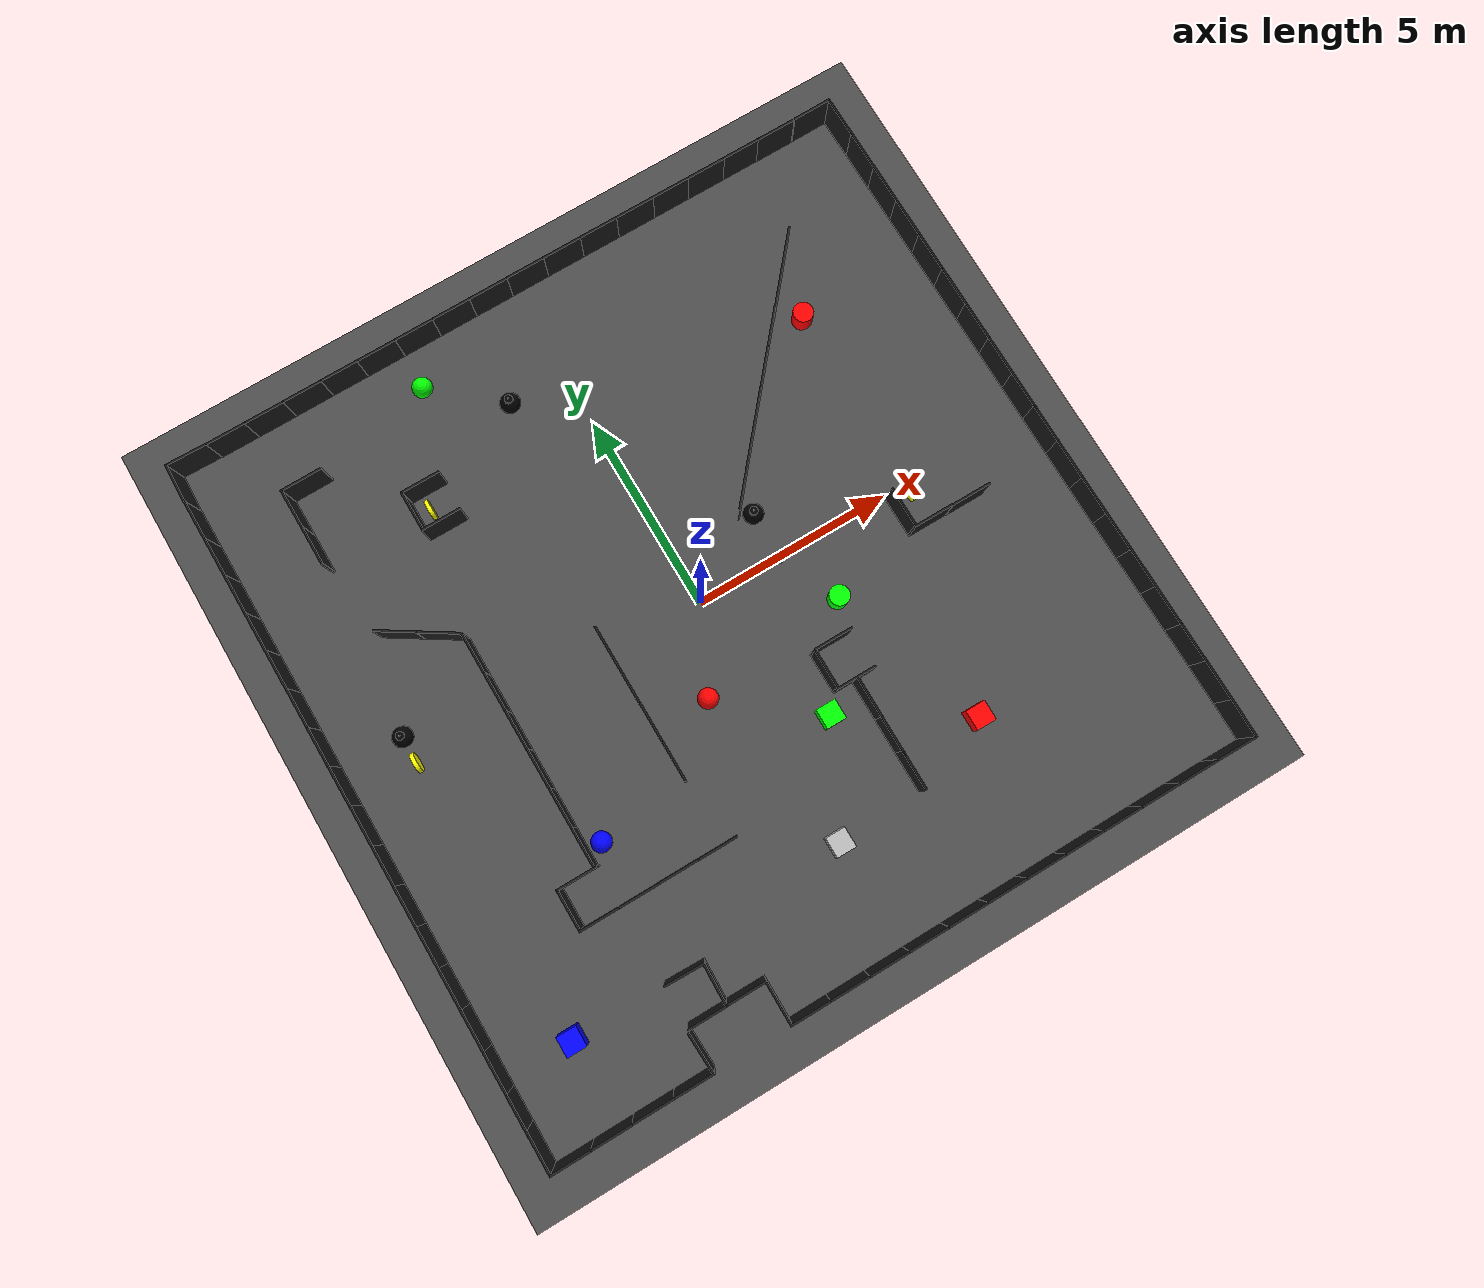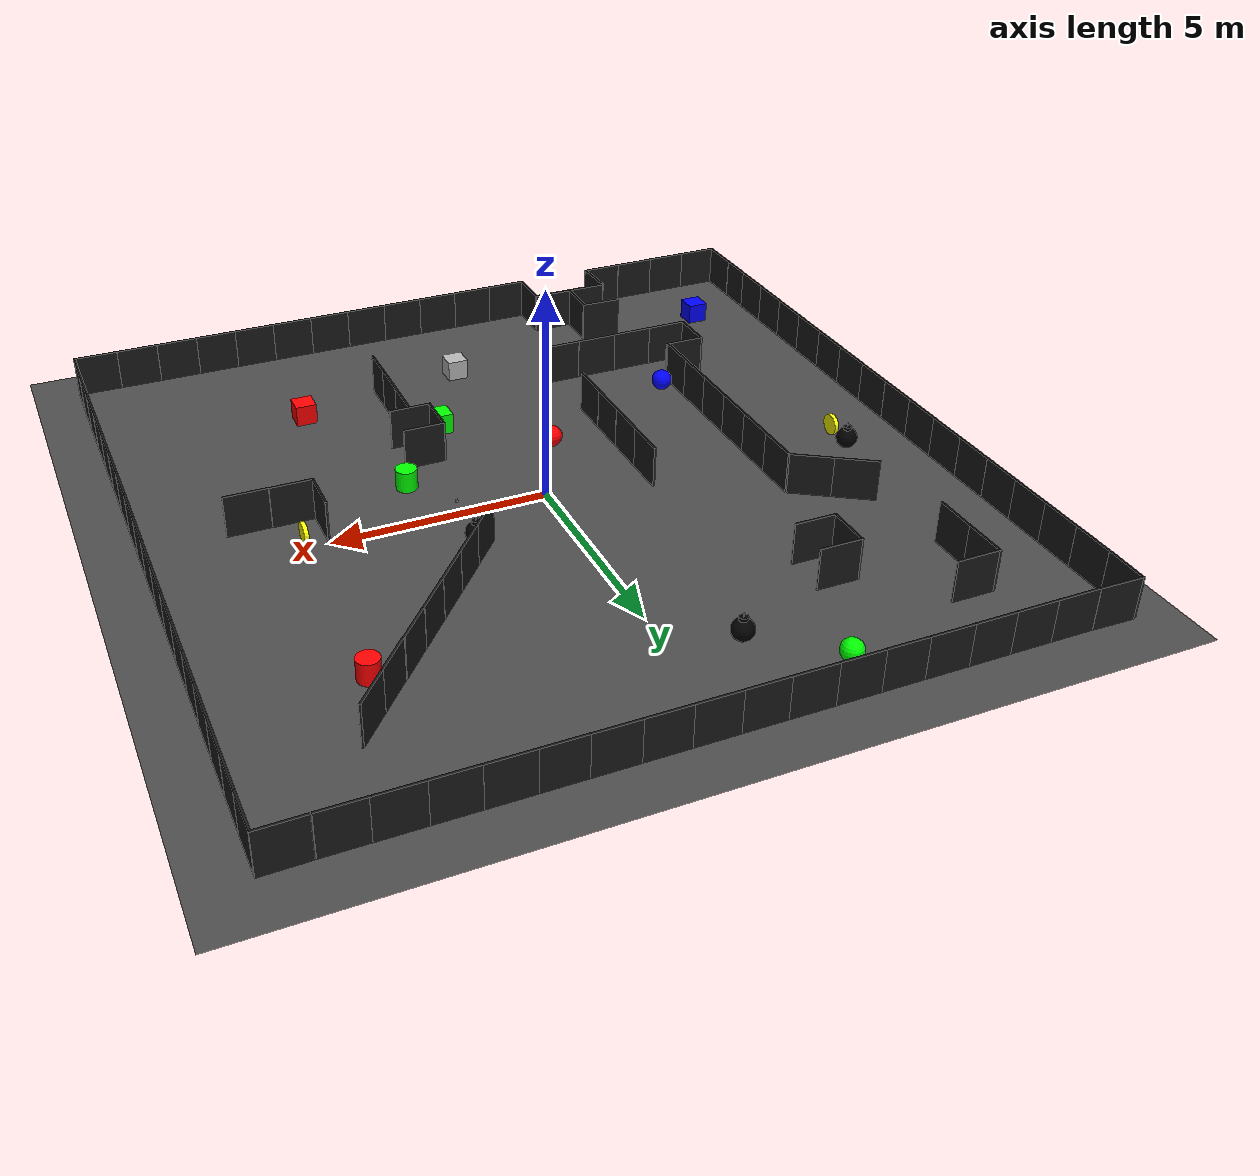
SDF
<sdf version="1.6">
 <world name="default">
  <model name="labrob_ground">
   <static>1</static>
   <link name="link">
    <collision name="collision">
     <geometry><plane><normal>0 0 1</normal><size>20 20</size></plane></geometry>
     <surface><friction><ode><mu>100</mu><mu2>50</mu2></ode></friction></surface>
    </collision>
    <visual name="visual">
     <cast_shadows>0</cast_shadows>
     <geometry><plane><normal>0 0 1</normal><size>20 20</size></plane></geometry>
     <material>
      <script>
       <uri>model://labrob_ground/materials/scripts/</uri>
       <uri>model://labrob_ground/materials/textures/</uri>
       <name>Labrob/AsphaltGround</name>
      </script>
     </material>
    </visual>
   </link>
  </model>
  <light name="sun" type="directional">
   <pose>0 0 10 0 -0 0</pose>
   <diffuse>0.8 0.8 0.8 1</diffuse>
   <specular>0.1 0.1 0.1 1</specular>
   <attenuation>
    <range>1000</range>
    <constant>0.9</constant>
    <linear>0.01</linear>
    <quadratic>0.001</quadratic>
   </attenuation>
   <direction>-0.5 0.5 -1</direction>
  </light>
  <model name="cube_red">
   <static>1</static>
   <link name="chassis">
    <pose>0 0 0.25 0 -0 0</pose>
    <collision name="collision"><geometry><box><size>0.5 0.5 0.5</size></box></geometry></collision>
    <visual name="visual">
     <geometry><box><size>0.5 0.5 0.5</size></box></geometry>
     <material>
      <ambient>1 0 0 1</ambient>
      <diffuse>1 0 0 1</diffuse>
      <specular>0.1 0.1 0.1 1</specular>
      <emissive>0 0 0 0</emissive>
     </material>
    </visual>
   </link>
   <pose>4.05938 -5.46614 0 0 -0 0</pose>
  </model>
  <model name="cube_blue">
   <static>1</static>
   <link name="chassis">
    <pose>0 0 0.25 0 -0 0</pose>
    <collision name="collision"><geometry><box><size>0.5 0.5 0.5</size></box></geometry></collision>
    <visual name="visual">
     <geometry><box><size>0.5 0.5 0.5</size></box></geometry>
     <material>
      <ambient>0 0 1 1</ambient>
      <diffuse>0 0 1 1</diffuse>
      <specular>0.1 0.1 0.1 1</specular>
      <emissive>0 0 0 0</emissive>
     </material>
    </visual>
   </link>
   <pose>-7.32238 -6.88227 0 0 -0 0</pose>
  </model>
  <model name="cube_green">
   <static>1</static>
   <link name="chassis">
    <pose>0 0 0.25 0 -0 0</pose>
    <collision name="collision"><geometry><box><size>0.5 0.5 0.5</size></box></geometry></collision>
    <visual name="visual">
     <geometry><box><size>0.5 0.5 0.5</size></box></geometry>
     <material>
      <ambient>0 1 0 1</ambient>
      <diffuse>0 1 0 1</diffuse>
      <specular>0.1 0.1 0.1 1</specular>
      <emissive>0 0 0 0</emissive>
     </material>
    </visual>
   </link>
   <pose>1.18468 -3.72596 0 0 -0 0</pose>
  </model>
  <model name="sphere_red">
   <static>1</static>
   <link name="chassis">
    <pose>0 0 0.25 0 -0 0</pose>
    <collision name="collision"><geometry><sphere><radius>0.25</radius></sphere></geometry></collision>
    <visual name="visual">
     <geometry><sphere><radius>0.25</radius></sphere></geometry>
     <material>
      <ambient>1 0 0 1</ambient>
      <diffuse>1 0 0 1</diffuse>
      <specular>0.1 0.1 0.1 1</specular>
      <emissive>0 0 0 0</emissive>
     </material>
    </visual>
   </link>
   <pose>-1 -2 0 0 -0 0</pose>
  </model>
  <model name="sphere_blue">
   <static>1</static>
   <link name="chassis">
    <pose>0 0 0.25 0 -0 0</pose>
    <collision name="collision"><geometry><sphere><radius>0.25</radius></sphere></geometry></collision>
    <visual name="visual">
     <geometry><sphere><radius>0.25</radius></sphere></geometry>
     <material>
      <ambient>0 0 1 1</ambient>
      <diffuse>0 0 1 1</diffuse>
      <specular>0.1 0.1 0.1 1</specular>
      <emissive>0 0 0 0</emissive>
     </material>
    </visual>
   </link>
   <pose>-4.67163 -3.53999 0 0 -0 0</pose>
  </model>
  <model name="sphere_green">
   <static>1</static>
   <link name="chassis">
    <pose>0 0 0.25 0 -0 0</pose>
    <collision name="collision"><geometry><sphere><radius>0.25</radius></sphere></geometry></collision>
    <visual name="visual">
     <geometry><sphere><radius>0.25</radius></sphere></geometry>
     <material>
      <ambient>0 1 0 1</ambient>
      <diffuse>0 1 0 1</diffuse>
      <specular>0.1 0.1 0.1 1</specular>
      <emissive>0 0 0 0</emissive>
     </material>
    </visual>
   </link>
   <pose>-3.05169 7.76717 0 0 -0 0</pose>
  </model>
  <model name="cylinder_red">
   <static>1</static>
   <link name="chassis">
    <pose>0 0 0.25 0 -0 0</pose>
    <collision name="collision">
     <geometry><cylinder><radius>0.25</radius><length>0.5</length></cylinder></geometry>
    </collision>
    <visual name="visual">
     <geometry><cylinder><radius>0.25</radius><length>0.5</length></cylinder></geometry>
     <material>
      <ambient>1 0 0 1</ambient>
      <diffuse>1 0 0 1</diffuse>
      <specular>0.1 0.1 0.1 1</specular>
      <emissive>0 0 0 0</emissive>
     </material>
    </visual>
   </link>
   <pose>5.60269 4.70393 0 0 -0 0</pose>
  </model>
  <model name="cylinder_green">
   <static>1</static>
   <link name="chassis">
    <pose>0 0 0.25 0 -0 0</pose>
    <collision name="collision">
     <geometry><cylinder><radius>0.25</radius><length>0.5</length></cylinder></geometry>
    </collision>
    <visual name="visual">
     <geometry><cylinder><radius>0.25</radius><length>0.5</length></cylinder></geometry>
     <material>
      <ambient>0 1 0 1</ambient>
      <diffuse>0 1 0 1</diffuse>
      <specular>0.1 0.1 0.1 1</specular>
      <emissive>0 0 0 0</emissive>
     </material>
    </visual>
   </link>
   <pose>2.76797 -1.52323 0 0 -0 0</pose>
  </model>
  <model name="barrier_1">
   <static>1</static>
   <link name="chassis">
    <pose>0 0 0.5 0 -0 0</pose>
    <collision name="collision"><geometry><box><size>1 0.05 1</size></box></geometry></collision>
    <visual name="visual">
     <geometry><box><size>1 0.05 1</size></box></geometry>
     <material>
      <ambient>0.1 0.1 0.1 1</ambient>
      <diffuse>0.1 0.1 0.1 1</diffuse>
      <specular>0.1 0.1 0.1 1</specular>
      <emissive>0 0 0 0</emissive>
     </material>
    </visual>
   </link>
   <pose>-4.49325 -4.95734 0 0 -0 0</pose>
  </model>
  <model name="coin">
   <static>1</static>
   <link name="chassis">
    <pose>0 0 0.25 0 -0 0</pose>
    <visual name="visual">
     <pose>0 0 0 0 1.57 0</pose>
     <geometry><cylinder><radius>0.25</radius><length>0.1</length></cylinder></geometry>
     <material>
      <ambient>1 1 0 1</ambient>
      <diffuse>1 1 0 1</diffuse>
      <specular>0.1 0.1 0.1 1</specular>
      <emissive>0 0 0 0</emissive>
     </material>
    </visual>
   </link>
   <pose>-4.29923 5.05802 0 0 -0 0</pose>
  </model>
  <model name="bomb">
   <static>1</static>
   <link name="chassis">
    <pose>0 0 0.25 0 -0 0</pose>
    <visual name="visual">
     <pose>0 0 0.2 0 -0 0</pose>
     <geometry><cylinder><radius>0.1</radius><length>0.2</length></cylinder></geometry>
     <material>
      <ambient>0 0 0 1</ambient>
      <diffuse>0 0 0 1</diffuse>
      <specular>0.1 0.1 0.1 1</specular>
      <emissive>0 0 0 0</emissive>
     </material>
    </visual>
    <visual name="visual2">
     <geometry><sphere><radius>0.25</radius></sphere></geometry>
     <material>
      <ambient>0 0 0 1</ambient>
      <diffuse>0 0 0 1</diffuse>
      <specular>0.1 0.1 0.1 1</specular>
      <emissive>0 0 0 0</emissive>
     </material>
    </visual>
    <visual name="visual3">
     <pose>0 0 0.3 0 -0 0</pose>
     <geometry><cylinder><radius>0.01</radius><length>0.2</length></cylinder></geometry>
     <material>
      <ambient>1 1 1 1</ambient>
      <diffuse>1 1 1 1</diffuse>
      <specular>0.1 0.1 0.1 1</specular>
      <emissive>0 0 0 0</emissive>
     </material>
    </visual>
   </link>
   <pose>-7.36891 0.771698 0 0 -0 0</pose>
  </model>
  <model name="aruco_cube">
   <static>1</static>
   <link name="chassis">
    <pose>0 0 0.25 0 -0 0</pose>
    <collision name="collision"><geometry><box><size>0.5 0.5 0.5</size></box></geometry></collision>
    <visual name="visual">
     <geometry><box><size>0.5 0.5 0.5</size></box></geometry>
     <material>
      <script>
       <uri>model://aruco_cube/materials/scripts</uri>
       <uri>model://aruco_cube/materials/textures</uri>
       <name>Aruco/Diffuse</name>
      </script>
     </material>
    </visual>
   </link>
   <pose>-0.117623 -6.25229 0 0 -0 0</pose>
  </model>
  <gravity>0 0 -9.8</gravity>
  <magnetic_field>6e-06 2.3e-05 -4.2e-05</magnetic_field>
  <atmosphere type="adiabatic"/>
  <physics name="default_physics" default="0" type="ode">
   <max_step_size>0.001</max_step_size>
   <real_time_factor>1</real_time_factor>
   <real_time_update_rate>1000</real_time_update_rate>
  </physics>
  <scene><ambient>0.4 0.4 0.4 1</ambient><background>0.7 0.7 0.7 1</background><shadows>1</shadows></scene>
  <spherical_coordinates>
   <surface_model>EARTH_WGS84</surface_model>
   <latitude_deg>0</latitude_deg>
   <longitude_deg>0</longitude_deg>
   <elevation>0</elevation>
   <heading_deg>0</heading_deg>
  </spherical_coordinates>
  <model name="barrier_1_0">
   <static>1</static>
   <link name="chassis">
    <pose>0 0 0.5 0 -0 0</pose>
    <collision name="collision"><geometry><box><size>1 0.05 1</size></box></geometry></collision>
    <visual name="visual">
     <geometry><box><size>1 0.05 1</size></box></geometry>
     <material>
      <ambient>0.1 0.1 0.1 1</ambient>
      <diffuse>0.1 0.1 0.1 1</diffuse>
      <specular>0.1 0.1 0.1 1</specular>
      <emissive>0 0 0 0</emissive>
     </material>
    </visual>
   </link>
   <pose>-8.94669 -7.56184 0 0 0 -1.56862</pose>
  </model>
  <model name="barrier_2_0">
   <static>1</static>
   <link name="chassis">
    <pose>0 0 0.5 0 -0 0</pose>
    <collision name="collision"><geometry><box><size>1 0.05 1</size></box></geometry></collision>
    <visual name="visual">
     <geometry><box><size>1 0.05 1</size></box></geometry>
     <material>
      <ambient>0.1 0.1 0.1 1</ambient>
      <diffuse>0.1 0.1 0.1 1</diffuse>
      <specular>0.1 0.1 0.1 1</specular>
      <emissive>0 0 0 0</emissive>
     </material>
    </visual>
    <collision name="collision2">
     <pose>-0.475 0.525 0 0 -0 1.57</pose>
     <geometry><box><size>1 0.05 1</size></box></geometry>
    </collision>
    <visual name="visual2">
     <pose>-0.475 0.525 0 0 -0 1.57</pose>
     <geometry><box><size>1 0.05 1</size></box></geometry>
     <material>
      <ambient>0.1 0.1 0.1 1</ambient>
      <diffuse>0.1 0.1 0.1 1</diffuse>
      <specular>0.1 0.1 0.1 1</specular>
      <emissive>0 0 0 0</emissive>
     </material>
    </visual>
   </link>
   <pose>-8.96223 8.34033 0 0 0 -1.59066</pose>
  </model>
  <model name="barrier_1_0_clone">
   <static>1</static>
   <link name="chassis">
    <pose>0 0 0.5 0 -0 0</pose>
    <collision name="collision"><geometry><box><size>1 0.05 1</size></box></geometry></collision>
    <visual name="visual">
     <geometry><box><size>1 0.05 1</size></box></geometry>
     <material>
      <ambient>0.1 0.1 0.1 1</ambient>
      <diffuse>0.1 0.1 0.1 1</diffuse>
      <specular>0.1 0.1 0.1 1</specular>
      <emissive>0 0 0 0</emissive>
     </material>
    </visual>
   </link>
   <pose>-8.94675 -6.56146 0 0 0 -1.56862</pose>
  </model>
  <model name="barrier_1_0_clone_0">
   <static>1</static>
   <link name="chassis">
    <pose>0 0 0.5 0 -0 0</pose>
    <collision name="collision"><geometry><box><size>1 0.05 1</size></box></geometry></collision>
    <visual name="visual">
     <geometry><box><size>1 0.05 1</size></box></geometry>
     <material>
      <ambient>0.1 0.1 0.1 1</ambient>
      <diffuse>0.1 0.1 0.1 1</diffuse>
      <specular>0.1 0.1 0.1 1</specular>
      <emissive>0 0 0 0</emissive>
     </material>
    </visual>
   </link>
   <pose>-8.94468 -5.56949 0 0 0 -1.56862</pose>
  </model>
  <model name="barrier_1_0_clone_1">
   <static>1</static>
   <link name="chassis">
    <pose>0 0 0.5 0 -0 0</pose>
    <collision name="collision"><geometry><box><size>1 0.05 1</size></box></geometry></collision>
    <visual name="visual">
     <geometry><box><size>1 0.05 1</size></box></geometry>
     <material>
      <ambient>0.1 0.1 0.1 1</ambient>
      <diffuse>0.1 0.1 0.1 1</diffuse>
      <specular>0.1 0.1 0.1 1</specular>
      <emissive>0 0 0 0</emissive>
     </material>
    </visual>
   </link>
   <pose>-8.94412 -4.57946 0 0 0 -1.56862</pose>
  </model>
  <model name="barrier_1_0_clone_2">
   <static>1</static>
   <link name="chassis">
    <pose>0 0 0.5 0 -0 0</pose>
    <collision name="collision"><geometry><box><size>1 0.05 1</size></box></geometry></collision>
    <visual name="visual">
     <geometry><box><size>1 0.05 1</size></box></geometry>
     <material>
      <ambient>0.1 0.1 0.1 1</ambient>
      <diffuse>0.1 0.1 0.1 1</diffuse>
      <specular>0.1 0.1 0.1 1</specular>
      <emissive>0 0 0 0</emissive>
     </material>
    </visual>
   </link>
   <pose>-8.94437 -3.58389 0 0 0 -1.56862</pose>
  </model>
  <model name="barrier_1_0_clone_3">
   <static>1</static>
   <link name="chassis">
    <pose>0 0 0.5 0 -0 0</pose>
    <collision name="collision"><geometry><box><size>1 0.05 1</size></box></geometry></collision>
    <visual name="visual">
     <geometry><box><size>1 0.05 1</size></box></geometry>
     <material>
      <ambient>0.1 0.1 0.1 1</ambient>
      <diffuse>0.1 0.1 0.1 1</diffuse>
      <specular>0.1 0.1 0.1 1</specular>
      <emissive>0 0 0 0</emissive>
     </material>
    </visual>
   </link>
   <pose>-8.94691 -2.58345 0 0 0 -1.56862</pose>
  </model>
  <model name="barrier_1_0_clone_4">
   <static>1</static>
   <link name="chassis">
    <pose>0 0 0.5 0 -0 0</pose>
    <collision name="collision"><geometry><box><size>1 0.05 1</size></box></geometry></collision>
    <visual name="visual">
     <geometry><box><size>1 0.05 1</size></box></geometry>
     <material>
      <ambient>0.1 0.1 0.1 1</ambient>
      <diffuse>0.1 0.1 0.1 1</diffuse>
      <specular>0.1 0.1 0.1 1</specular>
      <emissive>0 0 0 0</emissive>
     </material>
    </visual>
   </link>
   <pose>-8.94686 -1.591 0 0 0 -1.56862</pose>
  </model>
  <model name="barrier_1_0_clone_5">
   <static>1</static>
   <link name="chassis">
    <pose>0 0 0.5 0 -0 0</pose>
    <collision name="collision"><geometry><box><size>1 0.05 1</size></box></geometry></collision>
    <visual name="visual">
     <geometry><box><size>1 0.05 1</size></box></geometry>
     <material>
      <ambient>0.1 0.1 0.1 1</ambient>
      <diffuse>0.1 0.1 0.1 1</diffuse>
      <specular>0.1 0.1 0.1 1</specular>
      <emissive>0 0 0 0</emissive>
     </material>
    </visual>
   </link>
   <pose>-8.94828 -0.589978 0 0 0 -1.56862</pose>
  </model>
  <model name="barrier_1_0_clone_6">
   <static>1</static>
   <link name="chassis">
    <pose>0 0 0.5 0 -0 0</pose>
    <collision name="collision"><geometry><box><size>1 0.05 1</size></box></geometry></collision>
    <visual name="visual">
     <geometry><box><size>1 0.05 1</size></box></geometry>
     <material>
      <ambient>0.1 0.1 0.1 1</ambient>
      <diffuse>0.1 0.1 0.1 1</diffuse>
      <specular>0.1 0.1 0.1 1</specular>
      <emissive>0 0 0 0</emissive>
     </material>
    </visual>
   </link>
   <pose>-8.95339 0.409164 0 0 0 -1.56862</pose>
  </model>
  <model name="barrier_1_0_clone_7">
   <static>1</static>
   <link name="chassis">
    <pose>0 0 0.5 0 -0 0</pose>
    <collision name="collision"><geometry><box><size>1 0.05 1</size></box></geometry></collision>
    <visual name="visual">
     <geometry><box><size>1 0.05 1</size></box></geometry>
     <material>
      <ambient>0.1 0.1 0.1 1</ambient>
      <diffuse>0.1 0.1 0.1 1</diffuse>
      <specular>0.1 0.1 0.1 1</specular>
      <emissive>0 0 0 0</emissive>
     </material>
    </visual>
   </link>
   <pose>-8.95581 1.39827 0 0 0 -1.56862</pose>
  </model>
  <model name="barrier_1_0_clone_8">
   <static>1</static>
   <link name="chassis">
    <pose>0 0 0.5 0 -0 0</pose>
    <collision name="collision"><geometry><box><size>1 0.05 1</size></box></geometry></collision>
    <visual name="visual">
     <geometry><box><size>1 0.05 1</size></box></geometry>
     <material>
      <ambient>0.1 0.1 0.1 1</ambient>
      <diffuse>0.1 0.1 0.1 1</diffuse>
      <specular>0.1 0.1 0.1 1</specular>
      <emissive>0 0 0 0</emissive>
     </material>
    </visual>
   </link>
   <pose>-8.95548 2.3872 0 0 0 -1.56862</pose>
  </model>
  <model name="barrier_1_0_clone_9">
   <static>1</static>
   <link name="chassis">
    <pose>0 0 0.5 0 -0 0</pose>
    <collision name="collision"><geometry><box><size>1 0.05 1</size></box></geometry></collision>
    <visual name="visual">
     <geometry><box><size>1 0.05 1</size></box></geometry>
     <material>
      <ambient>0.1 0.1 0.1 1</ambient>
      <diffuse>0.1 0.1 0.1 1</diffuse>
      <specular>0.1 0.1 0.1 1</specular>
      <emissive>0 0 0 0</emissive>
     </material>
    </visual>
   </link>
   <pose>-8.95928 3.38028 0 0 0 -1.56862</pose>
  </model>
  <model name="barrier_1_0_clone_10">
   <static>1</static>
   <link name="chassis">
    <pose>0 0 0.5 0 -0 0</pose>
    <collision name="collision"><geometry><box><size>1 0.05 1</size></box></geometry></collision>
    <visual name="visual">
     <geometry><box><size>1 0.05 1</size></box></geometry>
     <material>
      <ambient>0.1 0.1 0.1 1</ambient>
      <diffuse>0.1 0.1 0.1 1</diffuse>
      <specular>0.1 0.1 0.1 1</specular>
      <emissive>0 0 0 0</emissive>
     </material>
    </visual>
   </link>
   <pose>-8.96389 4.36691 0 0 0 -1.56862</pose>
  </model>
  <model name="barrier_1_0_clone_11">
   <static>1</static>
   <link name="chassis">
    <pose>0 0 0.5 0 -0 0</pose>
    <collision name="collision"><geometry><box><size>1 0.05 1</size></box></geometry></collision>
    <visual name="visual">
     <geometry><box><size>1 0.05 1</size></box></geometry>
     <material>
      <ambient>0.1 0.1 0.1 1</ambient>
      <diffuse>0.1 0.1 0.1 1</diffuse>
      <specular>0.1 0.1 0.1 1</specular>
      <emissive>0 0 0 0</emissive>
     </material>
    </visual>
   </link>
   <pose>-8.96484 5.35736 0 0 0 -1.56862</pose>
  </model>
  <model name="barrier_1_0_clone_12">
   <static>1</static>
   <link name="chassis">
    <pose>0 0 0.5 0 -0 0</pose>
    <collision name="collision"><geometry><box><size>1 0.05 1</size></box></geometry></collision>
    <visual name="visual">
     <geometry><box><size>1 0.05 1</size></box></geometry>
     <material>
      <ambient>0.1 0.1 0.1 1</ambient>
      <diffuse>0.1 0.1 0.1 1</diffuse>
      <specular>0.1 0.1 0.1 1</specular>
      <emissive>0 0 0 0</emissive>
     </material>
    </visual>
   </link>
   <pose>-8.96737 6.34739 0 0 0 -1.56862</pose>
  </model>
  <model name="barrier_1_0_clone_13">
   <static>1</static>
   <link name="chassis">
    <pose>0 0 0.5 0 -0 0</pose>
    <collision name="collision"><geometry><box><size>1 0.05 1</size></box></geometry></collision>
    <visual name="visual">
     <geometry><box><size>1 0.05 1</size></box></geometry>
     <material>
      <ambient>0.1 0.1 0.1 1</ambient>
      <diffuse>0.1 0.1 0.1 1</diffuse>
      <specular>0.1 0.1 0.1 1</specular>
      <emissive>0 0 0 0</emissive>
     </material>
    </visual>
   </link>
   <pose>-8.96983 7.33788 0 0 0 -1.56862</pose>
  </model>
  <model name="barrier_1_18">
   <static>1</static>
   <link name="chassis">
    <pose>0 0 0.5 0 -0 0</pose>
    <collision name="collision"><geometry><box><size>1 0.05 1</size></box></geometry></collision>
    <visual name="visual">
     <geometry><box><size>1 0.05 1</size></box></geometry>
     <material>
      <ambient>0.1 0.1 0.1 1</ambient>
      <diffuse>0.1 0.1 0.1 1</diffuse>
      <specular>0.1 0.1 0.1 1</specular>
      <emissive>0 0 0 0</emissive>
     </material>
    </visual>
   </link>
   <pose>-7.43182 8.78835 0 0 -0 0</pose>
  </model>
  <model name="barrier_1_18_clone">
   <static>1</static>
   <link name="chassis">
    <pose>0 0 0.5 0 -0 0</pose>
    <collision name="collision"><geometry><box><size>1 0.05 1</size></box></geometry></collision>
    <visual name="visual">
     <geometry><box><size>1 0.05 1</size></box></geometry>
     <material>
      <ambient>0.1 0.1 0.1 1</ambient>
      <diffuse>0.1 0.1 0.1 1</diffuse>
      <specular>0.1 0.1 0.1 1</specular>
      <emissive>0 0 0 0</emissive>
     </material>
    </visual>
   </link>
   <pose>-6.45226 8.78729 0 0 -0 0</pose>
  </model>
  <model name="barrier_1_18_clone_0">
   <static>1</static>
   <link name="chassis">
    <pose>0 0 0.5 0 -0 0</pose>
    <collision name="collision"><geometry><box><size>1 0.05 1</size></box></geometry></collision>
    <visual name="visual">
     <geometry><box><size>1 0.05 1</size></box></geometry>
     <material>
      <ambient>0.1 0.1 0.1 1</ambient>
      <diffuse>0.1 0.1 0.1 1</diffuse>
      <specular>0.1 0.1 0.1 1</specular>
      <emissive>0 0 0 0</emissive>
     </material>
    </visual>
   </link>
   <pose>-5.46816 8.79079 0 0 -0 0</pose>
  </model>
  <model name="barrier_1_18_clone_1">
   <static>1</static>
   <link name="chassis">
    <pose>0 0 0.5 0 -0 0</pose>
    <collision name="collision"><geometry><box><size>1 0.05 1</size></box></geometry></collision>
    <visual name="visual">
     <geometry><box><size>1 0.05 1</size></box></geometry>
     <material>
      <ambient>0.1 0.1 0.1 1</ambient>
      <diffuse>0.1 0.1 0.1 1</diffuse>
      <specular>0.1 0.1 0.1 1</specular>
      <emissive>0 0 0 0</emissive>
     </material>
    </visual>
   </link>
   <pose>-4.50737 8.79381 0 0 -0 0</pose>
  </model>
  <model name="barrier_1_18_clone_2">
   <static>1</static>
   <link name="chassis">
    <pose>0 0 0.5 0 -0 0</pose>
    <collision name="collision"><geometry><box><size>1 0.05 1</size></box></geometry></collision>
    <visual name="visual">
     <geometry><box><size>1 0.05 1</size></box></geometry>
     <material>
      <ambient>0.1 0.1 0.1 1</ambient>
      <diffuse>0.1 0.1 0.1 1</diffuse>
      <specular>0.1 0.1 0.1 1</specular>
      <emissive>0 0 0 0</emissive>
     </material>
    </visual>
   </link>
   <pose>-3.53062 8.79201 0 0 -0 0</pose>
  </model>
  <model name="barrier_1_18_clone_3">
   <static>1</static>
   <link name="chassis">
    <pose>0 0 0.5 0 -0 0</pose>
    <collision name="collision"><geometry><box><size>1 0.05 1</size></box></geometry></collision>
    <visual name="visual">
     <geometry><box><size>1 0.05 1</size></box></geometry>
     <material>
      <ambient>0.1 0.1 0.1 1</ambient>
      <diffuse>0.1 0.1 0.1 1</diffuse>
      <specular>0.1 0.1 0.1 1</specular>
      <emissive>0 0 0 0</emissive>
     </material>
    </visual>
   </link>
   <pose>-2.54563 8.79444 0 0 -0 0</pose>
  </model>
  <model name="barrier_1_18_clone_4">
   <static>1</static>
   <link name="chassis">
    <pose>0 0 0.5 0 -0 0</pose>
    <collision name="collision"><geometry><box><size>1 0.05 1</size></box></geometry></collision>
    <visual name="visual">
     <geometry><box><size>1 0.05 1</size></box></geometry>
     <material>
      <ambient>0.1 0.1 0.1 1</ambient>
      <diffuse>0.1 0.1 0.1 1</diffuse>
      <specular>0.1 0.1 0.1 1</specular>
      <emissive>0 0 0 0</emissive>
     </material>
    </visual>
   </link>
   <pose>-1.55694 8.79631 0 0 -0 0</pose>
  </model>
  <model name="barrier_1_18_clone_5">
   <static>1</static>
   <link name="chassis">
    <pose>0 0 0.5 0 -0 0</pose>
    <collision name="collision"><geometry><box><size>1 0.05 1</size></box></geometry></collision>
    <visual name="visual">
     <geometry><box><size>1 0.05 1</size></box></geometry>
     <material>
      <ambient>0.1 0.1 0.1 1</ambient>
      <diffuse>0.1 0.1 0.1 1</diffuse>
      <specular>0.1 0.1 0.1 1</specular>
      <emissive>0 0 0 0</emissive>
     </material>
    </visual>
   </link>
   <pose>-0.565924 8.79602 0 0 -0 0</pose>
  </model>
  <model name="barrier_1_18_clone_6">
   <static>1</static>
   <link name="chassis">
    <pose>0 0 0.5 0 -0 0</pose>
    <collision name="collision"><geometry><box><size>1 0.05 1</size></box></geometry></collision>
    <visual name="visual">
     <geometry><box><size>1 0.05 1</size></box></geometry>
     <material>
      <ambient>0.1 0.1 0.1 1</ambient>
      <diffuse>0.1 0.1 0.1 1</diffuse>
      <specular>0.1 0.1 0.1 1</specular>
      <emissive>0 0 0 0</emissive>
     </material>
    </visual>
   </link>
   <pose>0.418427 8.79993 0 0 -0 0</pose>
  </model>
  <model name="barrier_1_18_clone_7">
   <static>1</static>
   <link name="chassis">
    <pose>0 0 0.5 0 -0 0</pose>
    <collision name="collision"><geometry><box><size>1 0.05 1</size></box></geometry></collision>
    <visual name="visual">
     <geometry><box><size>1 0.05 1</size></box></geometry>
     <material>
      <ambient>0.1 0.1 0.1 1</ambient>
      <diffuse>0.1 0.1 0.1 1</diffuse>
      <specular>0.1 0.1 0.1 1</specular>
      <emissive>0 0 0 0</emissive>
     </material>
    </visual>
   </link>
   <pose>1.40717 8.80045 0 0 -0 0</pose>
  </model>
  <model name="barrier_1_18_clone_8">
   <static>1</static>
   <link name="chassis">
    <pose>0 0 0.5 0 -0 0</pose>
    <collision name="collision"><geometry><box><size>1 0.05 1</size></box></geometry></collision>
    <visual name="visual">
     <geometry><box><size>1 0.05 1</size></box></geometry>
     <material>
      <ambient>0.1 0.1 0.1 1</ambient>
      <diffuse>0.1 0.1 0.1 1</diffuse>
      <specular>0.1 0.1 0.1 1</specular>
      <emissive>0 0 0 0</emissive>
     </material>
    </visual>
   </link>
   <pose>2.39968 8.80206 0 0 -0 0</pose>
  </model>
  <model name="barrier_1_18_clone_9">
   <static>1</static>
   <link name="chassis">
    <pose>0 0 0.5 0 -0 0</pose>
    <collision name="collision"><geometry><box><size>1 0.05 1</size></box></geometry></collision>
    <visual name="visual">
     <geometry><box><size>1 0.05 1</size></box></geometry>
     <material>
      <ambient>0.1 0.1 0.1 1</ambient>
      <diffuse>0.1 0.1 0.1 1</diffuse>
      <specular>0.1 0.1 0.1 1</specular>
      <emissive>0 0 0 0</emissive>
     </material>
    </visual>
   </link>
   <pose>3.38938 8.80144 0 0 -0 0</pose>
  </model>
  <model name="barrier_1_18_clone_10">
   <static>1</static>
   <link name="chassis">
    <pose>0 0 0.5 0 -0 0</pose>
    <collision name="collision"><geometry><box><size>1 0.05 1</size></box></geometry></collision>
    <visual name="visual">
     <geometry><box><size>1 0.05 1</size></box></geometry>
     <material>
      <ambient>0.1 0.1 0.1 1</ambient>
      <diffuse>0.1 0.1 0.1 1</diffuse>
      <specular>0.1 0.1 0.1 1</specular>
      <emissive>0 0 0 0</emissive>
     </material>
    </visual>
   </link>
   <pose>4.36187 8.80227 0 0 -0 0</pose>
  </model>
  <model name="barrier_1_18_clone_11">
   <static>1</static>
   <link name="chassis">
    <pose>0 0 0.5 0 -0 0</pose>
    <collision name="collision"><geometry><box><size>1 0.05 1</size></box></geometry></collision>
    <visual name="visual">
     <geometry><box><size>1 0.05 1</size></box></geometry>
     <material>
      <ambient>0.1 0.1 0.1 1</ambient>
      <diffuse>0.1 0.1 0.1 1</diffuse>
      <specular>0.1 0.1 0.1 1</specular>
      <emissive>0 0 0 0</emissive>
     </material>
    </visual>
   </link>
   <pose>5.34049 8.80006 0 0 -0 0</pose>
  </model>
  <model name="barrier_1_18_clone_12">
   <static>1</static>
   <link name="chassis">
    <pose>0 0 0.5 0 -0 0</pose>
    <collision name="collision"><geometry><box><size>1 0.05 1</size></box></geometry></collision>
    <visual name="visual">
     <geometry><box><size>1 0.05 1</size></box></geometry>
     <material>
      <ambient>0.1 0.1 0.1 1</ambient>
      <diffuse>0.1 0.1 0.1 1</diffuse>
      <specular>0.1 0.1 0.1 1</specular>
      <emissive>0 0 0 0</emissive>
     </material>
    </visual>
   </link>
   <pose>6.32592 8.80071 0 0 -0 0</pose>
  </model>
  <model name="barrier_1_19">
   <static>1</static>
   <link name="chassis">
    <pose>0 0 0.5 0 -0 0</pose>
    <collision name="collision"><geometry><box><size>1 0.05 1</size></box></geometry></collision>
    <visual name="visual">
     <geometry><box><size>1 0.05 1</size></box></geometry>
     <material>
      <ambient>0.1 0.1 0.1 1</ambient>
      <diffuse>0.1 0.1 0.1 1</diffuse>
      <specular>0.1 0.1 0.1 1</specular>
      <emissive>0 0 0 0</emissive>
     </material>
    </visual>
   </link>
   <pose>7.28219 8.79827 0 0 -0 0</pose>
  </model>
  <model name="barrier_2_4">
   <static>1</static>
   <link name="chassis">
    <pose>0 0 0.5 0 -0 0</pose>
    <collision name="collision"><geometry><box><size>1 0.05 1</size></box></geometry></collision>
    <visual name="visual">
     <geometry><box><size>1 0.05 1</size></box></geometry>
     <material>
      <ambient>0.1 0.1 0.1 1</ambient>
      <diffuse>0.1 0.1 0.1 1</diffuse>
      <specular>0.1 0.1 0.1 1</specular>
      <emissive>0 0 0 0</emissive>
     </material>
    </visual>
    <collision name="collision2">
     <pose>-0.475 0.525 0 0 -0 1.57</pose>
     <geometry><box><size>1 0.05 1</size></box></geometry>
    </collision>
    <visual name="visual2">
     <pose>-0.475 0.525 0 0 -0 1.57</pose>
     <geometry><box><size>1 0.05 1</size></box></geometry>
     <material>
      <ambient>0.1 0.1 0.1 1</ambient>
      <diffuse>0.1 0.1 0.1 1</diffuse>
      <specular>0.1 0.1 0.1 1</specular>
      <emissive>0 0 0 0</emissive>
     </material>
    </visual>
   </link>
   <pose>8.30821 8.80802 0 0 0 -3.12929</pose>
  </model>
  <model name="barrier_1_20">
   <static>1</static>
   <link name="chassis">
    <pose>0 0 0.5 0 -0 0</pose>
    <collision name="collision"><geometry><box><size>1 0.05 1</size></box></geometry></collision>
    <visual name="visual">
     <geometry><box><size>1 0.05 1</size></box></geometry>
     <material>
      <ambient>0.1 0.1 0.1 1</ambient>
      <diffuse>0.1 0.1 0.1 1</diffuse>
      <specular>0.1 0.1 0.1 1</specular>
      <emissive>0 0 0 0</emissive>
     </material>
    </visual>
   </link>
   <pose>8.79906 7.29147 0 0 -0 1.5774</pose>
  </model>
  <model name="barrier_1_20_clone">
   <static>1</static>
   <link name="chassis">
    <pose>0 0 0.5 0 -0 0</pose>
    <collision name="collision"><geometry><box><size>1 0.05 1</size></box></geometry></collision>
    <visual name="visual">
     <geometry><box><size>1 0.05 1</size></box></geometry>
     <material>
      <ambient>0.1 0.1 0.1 1</ambient>
      <diffuse>0.1 0.1 0.1 1</diffuse>
      <specular>0.1 0.1 0.1 1</specular>
      <emissive>0 0 0 0</emissive>
     </material>
    </visual>
   </link>
   <pose>8.80796 6.30422 0 0 -0 1.5774</pose>
  </model>
  <model name="barrier_1_20_clone_0">
   <static>1</static>
   <link name="chassis">
    <pose>0 0 0.5 0 -0 0</pose>
    <collision name="collision"><geometry><box><size>1 0.05 1</size></box></geometry></collision>
    <visual name="visual">
     <geometry><box><size>1 0.05 1</size></box></geometry>
     <material>
      <ambient>0.1 0.1 0.1 1</ambient>
      <diffuse>0.1 0.1 0.1 1</diffuse>
      <specular>0.1 0.1 0.1 1</specular>
      <emissive>0 0 0 0</emissive>
     </material>
    </visual>
   </link>
   <pose>8.81475 5.30463 0 0 -0 1.5774</pose>
  </model>
  <model name="barrier_1_20_clone_1">
   <static>1</static>
   <link name="chassis">
    <pose>0 0 0.5 0 -0 0</pose>
    <collision name="collision"><geometry><box><size>1 0.05 1</size></box></geometry></collision>
    <visual name="visual">
     <geometry><box><size>1 0.05 1</size></box></geometry>
     <material>
      <ambient>0.1 0.1 0.1 1</ambient>
      <diffuse>0.1 0.1 0.1 1</diffuse>
      <specular>0.1 0.1 0.1 1</specular>
      <emissive>0 0 0 0</emissive>
     </material>
    </visual>
   </link>
   <pose>8.82092 4.30479 0 0 -0 1.5774</pose>
  </model>
  <model name="barrier_1_20_clone_2">
   <static>1</static>
   <link name="chassis">
    <pose>0 0 0.5 0 -0 0</pose>
    <collision name="collision"><geometry><box><size>1 0.05 1</size></box></geometry></collision>
    <visual name="visual">
     <geometry><box><size>1 0.05 1</size></box></geometry>
     <material>
      <ambient>0.1 0.1 0.1 1</ambient>
      <diffuse>0.1 0.1 0.1 1</diffuse>
      <specular>0.1 0.1 0.1 1</specular>
      <emissive>0 0 0 0</emissive>
     </material>
    </visual>
   </link>
   <pose>8.82738 3.30464 0 0 -0 1.5774</pose>
  </model>
  <model name="barrier_1_20_clone_3">
   <static>1</static>
   <link name="chassis">
    <pose>0 0 0.5 0 -0 0</pose>
    <collision name="collision"><geometry><box><size>1 0.05 1</size></box></geometry></collision>
    <visual name="visual">
     <geometry><box><size>1 0.05 1</size></box></geometry>
     <material>
      <ambient>0.1 0.1 0.1 1</ambient>
      <diffuse>0.1 0.1 0.1 1</diffuse>
      <specular>0.1 0.1 0.1 1</specular>
      <emissive>0 0 0 0</emissive>
     </material>
    </visual>
   </link>
   <pose>8.8341 2.30957 0 0 -0 1.5774</pose>
  </model>
  <model name="barrier_1_20_clone_4">
   <static>1</static>
   <link name="chassis">
    <pose>0 0 0.5 0 -0 0</pose>
    <collision name="collision"><geometry><box><size>1 0.05 1</size></box></geometry></collision>
    <visual name="visual">
     <geometry><box><size>1 0.05 1</size></box></geometry>
     <material>
      <ambient>0.1 0.1 0.1 1</ambient>
      <diffuse>0.1 0.1 0.1 1</diffuse>
      <specular>0.1 0.1 0.1 1</specular>
      <emissive>0 0 0 0</emissive>
     </material>
    </visual>
   </link>
   <pose>8.83911 1.31974 0 0 -0 1.5774</pose>
  </model>
  <model name="barrier_1_20_clone_5">
   <static>1</static>
   <link name="chassis">
    <pose>0 0 0.5 0 -0 0</pose>
    <collision name="collision"><geometry><box><size>1 0.05 1</size></box></geometry></collision>
    <visual name="visual">
     <geometry><box><size>1 0.05 1</size></box></geometry>
     <material>
      <ambient>0.1 0.1 0.1 1</ambient>
      <diffuse>0.1 0.1 0.1 1</diffuse>
      <specular>0.1 0.1 0.1 1</specular>
      <emissive>0 0 0 0</emissive>
     </material>
    </visual>
   </link>
   <pose>8.84496 0.320482 0 0 -0 1.5774</pose>
  </model>
  <model name="barrier_1_20_clone_6">
   <static>1</static>
   <link name="chassis">
    <pose>0 0 0.5 0 -0 0</pose>
    <collision name="collision"><geometry><box><size>1 0.05 1</size></box></geometry></collision>
    <visual name="visual">
     <geometry><box><size>1 0.05 1</size></box></geometry>
     <material>
      <ambient>0.1 0.1 0.1 1</ambient>
      <diffuse>0.1 0.1 0.1 1</diffuse>
      <specular>0.1 0.1 0.1 1</specular>
      <emissive>0 0 0 0</emissive>
     </material>
    </visual>
   </link>
   <pose>8.84728 -0.58686 0 0 -0 1.5774</pose>
  </model>
  <model name="barrier_1_20_clone_7">
   <static>1</static>
   <link name="chassis">
    <pose>0 0 0.5 0 -0 0</pose>
    <collision name="collision"><geometry><box><size>1 0.05 1</size></box></geometry></collision>
    <visual name="visual">
     <geometry><box><size>1 0.05 1</size></box></geometry>
     <material>
      <ambient>0.1 0.1 0.1 1</ambient>
      <diffuse>0.1 0.1 0.1 1</diffuse>
      <specular>0.1 0.1 0.1 1</specular>
      <emissive>0 0 0 0</emissive>
     </material>
    </visual>
   </link>
   <pose>8.85207 -1.56694 0 0 -0 1.5774</pose>
  </model>
  <model name="barrier_1_20_clone_8">
   <static>1</static>
   <link name="chassis">
    <pose>0 0 0.5 0 -0 0</pose>
    <collision name="collision"><geometry><box><size>1 0.05 1</size></box></geometry></collision>
    <visual name="visual">
     <geometry><box><size>1 0.05 1</size></box></geometry>
     <material>
      <ambient>0.1 0.1 0.1 1</ambient>
      <diffuse>0.1 0.1 0.1 1</diffuse>
      <specular>0.1 0.1 0.1 1</specular>
      <emissive>0 0 0 0</emissive>
     </material>
    </visual>
   </link>
   <pose>8.85973 -2.55147 0 0 -0 1.5774</pose>
  </model>
  <model name="barrier_1_20_clone_9">
   <static>1</static>
   <link name="chassis">
    <pose>0 0 0.5 0 -0 0</pose>
    <collision name="collision"><geometry><box><size>1 0.05 1</size></box></geometry></collision>
    <visual name="visual">
     <geometry><box><size>1 0.05 1</size></box></geometry>
     <material>
      <ambient>0.1 0.1 0.1 1</ambient>
      <diffuse>0.1 0.1 0.1 1</diffuse>
      <specular>0.1 0.1 0.1 1</specular>
      <emissive>0 0 0 0</emissive>
     </material>
    </visual>
   </link>
   <pose>8.86823 -3.52285 0 0 -0 1.5774</pose>
  </model>
  <model name="barrier_1_20_clone_10">
   <static>1</static>
   <link name="chassis">
    <pose>0 0 0.5 0 -0 0</pose>
    <collision name="collision"><geometry><box><size>1 0.05 1</size></box></geometry></collision>
    <visual name="visual">
     <geometry><box><size>1 0.05 1</size></box></geometry>
     <material>
      <ambient>0.1 0.1 0.1 1</ambient>
      <diffuse>0.1 0.1 0.1 1</diffuse>
      <specular>0.1 0.1 0.1 1</specular>
      <emissive>0 0 0 0</emissive>
     </material>
    </visual>
   </link>
   <pose>8.87802 -4.50707 0 0 -0 1.5774</pose>
  </model>
  <model name="barrier_1_20_clone_11">
   <static>1</static>
   <link name="chassis">
    <pose>0 0 0.5 0 -0 0</pose>
    <collision name="collision"><geometry><box><size>1 0.05 1</size></box></geometry></collision>
    <visual name="visual">
     <geometry><box><size>1 0.05 1</size></box></geometry>
     <material>
      <ambient>0.1 0.1 0.1 1</ambient>
      <diffuse>0.1 0.1 0.1 1</diffuse>
      <specular>0.1 0.1 0.1 1</specular>
      <emissive>0 0 0 0</emissive>
     </material>
    </visual>
   </link>
   <pose>8.88509 -5.50374 0 0 -0 1.5774</pose>
  </model>
  <model name="barrier_1_20_clone_12">
   <static>1</static>
   <link name="chassis">
    <pose>0 0 0.5 0 -0 0</pose>
    <collision name="collision"><geometry><box><size>1 0.05 1</size></box></geometry></collision>
    <visual name="visual">
     <geometry><box><size>1 0.05 1</size></box></geometry>
     <material>
      <ambient>0.1 0.1 0.1 1</ambient>
      <diffuse>0.1 0.1 0.1 1</diffuse>
      <specular>0.1 0.1 0.1 1</specular>
      <emissive>0 0 0 0</emissive>
     </material>
    </visual>
   </link>
   <pose>8.89388 -6.49549 0 0 -0 1.5774</pose>
  </model>
  <model name="barrier_1_20_clone_13">
   <static>1</static>
   <link name="chassis">
    <pose>0 0 0.5 0 -0 0</pose>
    <collision name="collision"><geometry><box><size>1 0.05 1</size></box></geometry></collision>
    <visual name="visual">
     <geometry><box><size>1 0.05 1</size></box></geometry>
     <material>
      <ambient>0.1 0.1 0.1 1</ambient>
      <diffuse>0.1 0.1 0.1 1</diffuse>
      <specular>0.1 0.1 0.1 1</specular>
      <emissive>0 0 0 0</emissive>
     </material>
    </visual>
   </link>
   <pose>8.89962 -7.46788 0 0 -0 1.5774</pose>
  </model>
  <model name="barrier_2_5">
   <static>1</static>
   <link name="chassis">
    <pose>0 0 0.5 0 -0 0</pose>
    <collision name="collision"><geometry><box><size>1 0.05 1</size></box></geometry></collision>
    <visual name="visual">
     <geometry><box><size>1 0.05 1</size></box></geometry>
     <material>
      <ambient>0.1 0.1 0.1 1</ambient>
      <diffuse>0.1 0.1 0.1 1</diffuse>
      <specular>0.1 0.1 0.1 1</specular>
      <emissive>0 0 0 0</emissive>
     </material>
    </visual>
    <collision name="collision2">
     <pose>-0.475 0.525 0 0 -0 1.57</pose>
     <geometry><box><size>1 0.05 1</size></box></geometry>
    </collision>
    <visual name="visual2">
     <pose>-0.475 0.525 0 0 -0 1.57</pose>
     <geometry><box><size>1 0.05 1</size></box></geometry>
     <material>
      <ambient>0.1 0.1 0.1 1</ambient>
      <diffuse>0.1 0.1 0.1 1</diffuse>
      <specular>0.1 0.1 0.1 1</specular>
      <emissive>0 0 0 0</emissive>
     </material>
    </visual>
   </link>
   <pose>8.89974 -8.45646 0 0 -0 1.56067</pose>
  </model>
  <model name="barrier_1_21">
   <static>1</static>
   <link name="chassis">
    <pose>0 0 0.5 0 -0 0</pose>
    <collision name="collision"><geometry><box><size>1 0.05 1</size></box></geometry></collision>
    <visual name="visual">
     <geometry><box><size>1 0.05 1</size></box></geometry>
     <material>
      <ambient>0.1 0.1 0.1 1</ambient>
      <diffuse>0.1 0.1 0.1 1</diffuse>
      <specular>0.1 0.1 0.1 1</specular>
      <emissive>0 0 0 0</emissive>
     </material>
    </visual>
   </link>
   <pose>7.3703 -8.92106 0 0 -0 0</pose>
  </model>
  <model name="barrier_1_21_clone">
   <static>1</static>
   <link name="chassis">
    <pose>0 0 0.5 0 -0 0</pose>
    <collision name="collision"><geometry><box><size>1 0.05 1</size></box></geometry></collision>
    <visual name="visual">
     <geometry><box><size>1 0.05 1</size></box></geometry>
     <material>
      <ambient>0.1 0.1 0.1 1</ambient>
      <diffuse>0.1 0.1 0.1 1</diffuse>
      <specular>0.1 0.1 0.1 1</specular>
      <emissive>0 0 0 0</emissive>
     </material>
    </visual>
   </link>
   <pose>6.37587 -8.91844 0 0 -0 0</pose>
  </model>
  <model name="barrier_1_21_clone_0">
   <static>1</static>
   <link name="chassis">
    <pose>0 0 0.5 0 -0 0</pose>
    <collision name="collision"><geometry><box><size>1 0.05 1</size></box></geometry></collision>
    <visual name="visual">
     <geometry><box><size>1 0.05 1</size></box></geometry>
     <material>
      <ambient>0.1 0.1 0.1 1</ambient>
      <diffuse>0.1 0.1 0.1 1</diffuse>
      <specular>0.1 0.1 0.1 1</specular>
      <emissive>0 0 0 0</emissive>
     </material>
    </visual>
   </link>
   <pose>5.38091 -8.91901 0 0 -0 0</pose>
  </model>
  <model name="barrier_1_21_clone_1">
   <static>1</static>
   <link name="chassis">
    <pose>0 0 0.5 0 -0 0</pose>
    <collision name="collision"><geometry><box><size>1 0.05 1</size></box></geometry></collision>
    <visual name="visual">
     <geometry><box><size>1 0.05 1</size></box></geometry>
     <material>
      <ambient>0.1 0.1 0.1 1</ambient>
      <diffuse>0.1 0.1 0.1 1</diffuse>
      <specular>0.1 0.1 0.1 1</specular>
      <emissive>0 0 0 0</emissive>
     </material>
    </visual>
   </link>
   <pose>4.38412 -8.919 0 0 -0 0</pose>
  </model>
  <model name="barrier_1_21_clone_2">
   <static>1</static>
   <link name="chassis">
    <pose>0 0 0.5 0 -0 0</pose>
    <collision name="collision"><geometry><box><size>1 0.05 1</size></box></geometry></collision>
    <visual name="visual">
     <geometry><box><size>1 0.05 1</size></box></geometry>
     <material>
      <ambient>0.1 0.1 0.1 1</ambient>
      <diffuse>0.1 0.1 0.1 1</diffuse>
      <specular>0.1 0.1 0.1 1</specular>
      <emissive>0 0 0 0</emissive>
     </material>
    </visual>
   </link>
   <pose>3.3874 -8.91868 0 0 -0 0</pose>
  </model>
  <model name="barrier_1_21_clone_3">
   <static>1</static>
   <link name="chassis">
    <pose>0 0 0.5 0 -0 0</pose>
    <collision name="collision"><geometry><box><size>1 0.05 1</size></box></geometry></collision>
    <visual name="visual">
     <geometry><box><size>1 0.05 1</size></box></geometry>
     <material>
      <ambient>0.1 0.1 0.1 1</ambient>
      <diffuse>0.1 0.1 0.1 1</diffuse>
      <specular>0.1 0.1 0.1 1</specular>
      <emissive>0 0 0 0</emissive>
     </material>
    </visual>
   </link>
   <pose>2.39009 -8.91902 0 0 -0 0</pose>
  </model>
  <model name="barrier_1_21_clone_4">
   <static>1</static>
   <link name="chassis">
    <pose>0 0 0.5 0 -0 0</pose>
    <collision name="collision"><geometry><box><size>1 0.05 1</size></box></geometry></collision>
    <visual name="visual">
     <geometry><box><size>1 0.05 1</size></box></geometry>
     <material>
      <ambient>0.1 0.1 0.1 1</ambient>
      <diffuse>0.1 0.1 0.1 1</diffuse>
      <specular>0.1 0.1 0.1 1</specular>
      <emissive>0 0 0 0</emissive>
     </material>
    </visual>
   </link>
   <pose>1.3925 -8.92038 0 0 -0 0</pose>
  </model>
  <model name="barrier_1_21_clone_5">
   <static>1</static>
   <link name="chassis">
    <pose>0 0 0.5 0 -0 0</pose>
    <collision name="collision"><geometry><box><size>1 0.05 1</size></box></geometry></collision>
    <visual name="visual">
     <geometry><box><size>1 0.05 1</size></box></geometry>
     <material>
      <ambient>0.1 0.1 0.1 1</ambient>
      <diffuse>0.1 0.1 0.1 1</diffuse>
      <specular>0.1 0.1 0.1 1</specular>
      <emissive>0 0 0 0</emissive>
     </material>
    </visual>
   </link>
   <pose>0.392966 -8.92228 0 0 -0 0</pose>
  </model>
  <model name="barrier_1_21_clone_6">
   <static>1</static>
   <link name="chassis">
    <pose>0 0 0.5 0 -0 0</pose>
    <collision name="collision"><geometry><box><size>1 0.05 1</size></box></geometry></collision>
    <visual name="visual">
     <geometry><box><size>1 0.05 1</size></box></geometry>
     <material>
      <ambient>0.1 0.1 0.1 1</ambient>
      <diffuse>0.1 0.1 0.1 1</diffuse>
      <specular>0.1 0.1 0.1 1</specular>
      <emissive>0 0 0 0</emissive>
     </material>
    </visual>
   </link>
   <pose>-0.5994 -8.92388 0 0 -0 0</pose>
  </model>
  <model name="barrier_1_21_clone_7">
   <static>1</static>
   <link name="chassis">
    <pose>0 0 0.5 0 -0 0</pose>
    <collision name="collision"><geometry><box><size>1 0.05 1</size></box></geometry></collision>
    <visual name="visual">
     <geometry><box><size>1 0.05 1</size></box></geometry>
     <material>
      <ambient>0.1 0.1 0.1 1</ambient>
      <diffuse>0.1 0.1 0.1 1</diffuse>
      <specular>0.1 0.1 0.1 1</specular>
      <emissive>0 0 0 0</emissive>
     </material>
    </visual>
   </link>
   <pose>-1.59182 -8.92491 0 0 -0 0</pose>
  </model>
  <model name="barrier_1_21_clone_8">
   <static>1</static>
   <link name="chassis">
    <pose>0 0 0.5 0 -0 0</pose>
    <collision name="collision"><geometry><box><size>1 0.05 1</size></box></geometry></collision>
    <visual name="visual">
     <geometry><box><size>1 0.05 1</size></box></geometry>
     <material>
      <ambient>0.1 0.1 0.1 1</ambient>
      <diffuse>0.1 0.1 0.1 1</diffuse>
      <specular>0.1 0.1 0.1 1</specular>
      <emissive>0 0 0 0</emissive>
     </material>
    </visual>
   </link>
   <pose>-3.55058 -7.87618 0 0 -0 0</pose>
  </model>
  <model name="barrier_1_21_clone_9">
   <static>1</static>
   <link name="chassis">
    <pose>0 0 0.5 0 -0 0</pose>
    <collision name="collision"><geometry><box><size>1 0.05 1</size></box></geometry></collision>
    <visual name="visual">
     <geometry><box><size>1 0.05 1</size></box></geometry>
     <material>
      <ambient>0.1 0.1 0.1 1</ambient>
      <diffuse>0.1 0.1 0.1 1</diffuse>
      <specular>0.1 0.1 0.1 1</specular>
      <emissive>0 0 0 0</emissive>
     </material>
    </visual>
   </link>
   <pose>-4.51155 -7.88119 0 0 -0 0</pose>
  </model>
  <model name="barrier_1_21_clone_10">
   <static>1</static>
   <link name="chassis">
    <pose>0 0 0.5 0 -0 0</pose>
    <collision name="collision"><geometry><box><size>1 0.05 1</size></box></geometry></collision>
    <visual name="visual">
     <geometry><box><size>1 0.05 1</size></box></geometry>
     <material>
      <ambient>0.1 0.1 0.1 1</ambient>
      <diffuse>0.1 0.1 0.1 1</diffuse>
      <specular>0.1 0.1 0.1 1</specular>
      <emissive>0 0 0 0</emissive>
     </material>
    </visual>
   </link>
   <pose>-5.00714 -8.42807 0 0 -0 1.61395</pose>
  </model>
  <model name="barrier_1_21_clone_11">
   <static>1</static>
   <link name="chassis">
    <pose>0 0 0.5 0 -0 0</pose>
    <collision name="collision"><geometry><box><size>1 0.05 1</size></box></geometry></collision>
    <visual name="visual">
     <geometry><box><size>1 0.05 1</size></box></geometry>
     <material>
      <ambient>0.1 0.1 0.1 1</ambient>
      <diffuse>0.1 0.1 0.1 1</diffuse>
      <specular>0.1 0.1 0.1 1</specular>
      <emissive>0 0 0 0</emissive>
     </material>
    </visual>
   </link>
   <pose>-5.46256 -8.9219 0 0 -0 0</pose>
  </model>
  <model name="barrier_1_21_clone_12">
   <static>1</static>
   <link name="chassis">
    <pose>0 0 0.5 0 -0 0</pose>
    <collision name="collision"><geometry><box><size>1 0.05 1</size></box></geometry></collision>
    <visual name="visual">
     <geometry><box><size>1 0.05 1</size></box></geometry>
     <material>
      <ambient>0.1 0.1 0.1 1</ambient>
      <diffuse>0.1 0.1 0.1 1</diffuse>
      <specular>0.1 0.1 0.1 1</specular>
      <emissive>0 0 0 0</emissive>
     </material>
    </visual>
   </link>
   <pose>-6.46593 -8.92117 0 0 -0 0</pose>
  </model>
  <model name="barrier_1_21_clone_13">
   <static>1</static>
   <link name="chassis">
    <pose>0 0 0.5 0 -0 0</pose>
    <collision name="collision"><geometry><box><size>1 0.05 1</size></box></geometry></collision>
    <visual name="visual">
     <geometry><box><size>1 0.05 1</size></box></geometry>
     <material>
      <ambient>0.1 0.1 0.1 1</ambient>
      <diffuse>0.1 0.1 0.1 1</diffuse>
      <specular>0.1 0.1 0.1 1</specular>
      <emissive>0 0 0 0</emissive>
     </material>
    </visual>
   </link>
   <pose>-7.46706 -8.92746 0 0 -0 0</pose>
  </model>
  <model name="barrier_2_6">
   <static>1</static>
   <link name="chassis">
    <pose>0 0 0.5 0 -0 0</pose>
    <collision name="collision"><geometry><box><size>1 0.05 1</size></box></geometry></collision>
    <visual name="visual">
     <geometry><box><size>1 0.05 1</size></box></geometry>
     <material>
      <ambient>0.1 0.1 0.1 1</ambient>
      <diffuse>0.1 0.1 0.1 1</diffuse>
      <specular>0.1 0.1 0.1 1</specular>
      <emissive>0 0 0 0</emissive>
     </material>
    </visual>
    <collision name="collision2">
     <pose>-0.475 0.525 0 0 -0 1.57</pose>
     <geometry><box><size>1 0.05 1</size></box></geometry>
    </collision>
    <visual name="visual2">
     <pose>-0.475 0.525 0 0 -0 1.57</pose>
     <geometry><box><size>1 0.05 1</size></box></geometry>
     <material>
      <ambient>0.1 0.1 0.1 1</ambient>
      <diffuse>0.1 0.1 0.1 1</diffuse>
      <specular>0.1 0.1 0.1 1</specular>
      <emissive>0 0 0 0</emissive>
     </material>
    </visual>
   </link>
   <pose>-8.46687 -8.92868 0 0 -0 0</pose>
  </model>
  <model name="barrier_2_7">
   <static>1</static>
   <link name="chassis">
    <pose>0 0 0.5 0 -0 0</pose>
    <collision name="collision"><geometry><box><size>1 0.05 1</size></box></geometry></collision>
    <visual name="visual">
     <geometry><box><size>1 0.05 1</size></box></geometry>
     <material>
      <ambient>0.1 0.1 0.1 1</ambient>
      <diffuse>0.1 0.1 0.1 1</diffuse>
      <specular>0.1 0.1 0.1 1</specular>
      <emissive>0 0 0 0</emissive>
     </material>
    </visual>
    <collision name="collision2">
     <pose>-0.475 0.525 0 0 -0 1.57</pose>
     <geometry><box><size>1 0.05 1</size></box></geometry>
    </collision>
    <visual name="visual2">
     <pose>-0.475 0.525 0 0 -0 1.57</pose>
     <geometry><box><size>1 0.05 1</size></box></geometry>
     <material>
      <ambient>0.1 0.1 0.1 1</ambient>
      <diffuse>0.1 0.1 0.1 1</diffuse>
      <specular>0.1 0.1 0.1 1</specular>
      <emissive>0 0 0 0</emissive>
     </material>
    </visual>
   </link>
   <pose>-2.5925 -8.92494 0 0 -0 0</pose>
  </model>
  <model name="barrier_2_8">
   <static>1</static>
   <link name="chassis">
    <pose>0 0 0.5 0 -0 0</pose>
    <collision name="collision"><geometry><box><size>1 0.05 1</size></box></geometry></collision>
    <visual name="visual">
     <geometry><box><size>1 0.05 1</size></box></geometry>
     <material>
      <ambient>0.1 0.1 0.1 1</ambient>
      <diffuse>0.1 0.1 0.1 1</diffuse>
      <specular>0.1 0.1 0.1 1</specular>
      <emissive>0 0 0 0</emissive>
     </material>
    </visual>
    <collision name="collision2">
     <pose>-0.475 0.525 0 0 -0 1.57</pose>
     <geometry><box><size>1 0.05 1</size></box></geometry>
    </collision>
    <visual name="visual2">
     <pose>-0.475 0.525 0 0 -0 1.57</pose>
     <geometry><box><size>1 0.05 1</size></box></geometry>
     <material>
      <ambient>0.1 0.1 0.1 1</ambient>
      <diffuse>0.1 0.1 0.1 1</diffuse>
      <specular>0.1 0.1 0.1 1</specular>
      <emissive>0 0 0 0</emissive>
     </material>
    </visual>
   </link>
   <pose>-4.49582 -6.87089 0 0 -0 3.11565</pose>
  </model>
  <model name="barrier_3_0">
   <static>1</static>
   <link name="chassis">
    <pose>0 0 0.5 0 -0 0</pose>
    <collision name="collision"><geometry><box><size>1 0.05 1</size></box></geometry></collision>
    <visual name="visual">
     <geometry><box><size>1 0.05 1</size></box></geometry>
     <material>
      <ambient>0.1 0.1 0.1 1</ambient>
      <diffuse>0.1 0.1 0.1 1</diffuse>
      <specular>0.1 0.1 0.1 1</specular>
      <emissive>0 0 0 0</emissive>
     </material>
    </visual>
    <collision name="collision2">
     <pose>-0.475 0.525 0 0 -0 1.57</pose>
     <geometry><box><size>1 0.05 1</size></box></geometry>
    </collision>
    <visual name="visual2">
     <pose>-0.475 0.525 0 0 -0 1.57</pose>
     <geometry><box><size>1 0.05 1</size></box></geometry>
     <material>
      <ambient>0.1 0.1 0.1 1</ambient>
      <diffuse>0.1 0.1 0.1 1</diffuse>
      <specular>0.1 0.1 0.1 1</specular>
      <emissive>0 0 0 0</emissive>
     </material>
    </visual>
    <collision name="collision3">
     <pose>0 1 0 0 -0 0</pose>
     <geometry><box><size>1 0.05 1</size></box></geometry>
    </collision>
    <visual name="visual3">
     <pose>0 1 0 0 -0 0</pose>
     <geometry><box><size>1 0.05 1</size></box></geometry>
     <material>
      <ambient>0.1 0.1 0.1 1</ambient>
      <diffuse>0.1 0.1 0.1 1</diffuse>
      <specular>0.1 0.1 0.1 1</specular>
      <emissive>0 0 0 0</emissive>
     </material>
    </visual>
   </link>
   <pose>-5.48365 -4.95486 0 0 -0 0</pose>
  </model>
  <model name="barrier_1_22">
   <static>1</static>
   <link name="chassis">
    <pose>0 0 0.5 0 -0 0</pose>
    <collision name="collision"><geometry><box><size>1 0.05 1</size></box></geometry></collision>
    <visual name="visual">
     <geometry><box><size>1 0.05 1</size></box></geometry>
     <material>
      <ambient>0.1 0.1 0.1 1</ambient>
      <diffuse>0.1 0.1 0.1 1</diffuse>
      <specular>0.1 0.1 0.1 1</specular>
      <emissive>0 0 0 0</emissive>
     </material>
    </visual>
   </link>
   <pose>-3.49746 -4.95231 0 0 -0 0</pose>
  </model>
  <model name="barrier_1_23">
   <static>1</static>
   <link name="chassis">
    <pose>0 0 0.5 0 -0 0</pose>
    <collision name="collision"><geometry><box><size>1 0.05 1</size></box></geometry></collision>
    <visual name="visual">
     <geometry><box><size>1 0.05 1</size></box></geometry>
     <material>
      <ambient>0.1 0.1 0.1 1</ambient>
      <diffuse>0.1 0.1 0.1 1</diffuse>
      <specular>0.1 0.1 0.1 1</specular>
      <emissive>0 0 0 0</emissive>
     </material>
    </visual>
   </link>
   <pose>-2.52236 -4.95576 0 0 -0 0</pose>
  </model>
  <model name="barrier_1_24">
   <static>1</static>
   <link name="chassis">
    <pose>0 0 0.5 0 -0 0</pose>
    <collision name="collision"><geometry><box><size>1 0.05 1</size></box></geometry></collision>
    <visual name="visual">
     <geometry><box><size>1 0.05 1</size></box></geometry>
     <material>
      <ambient>0.1 0.1 0.1 1</ambient>
      <diffuse>0.1 0.1 0.1 1</diffuse>
      <specular>0.1 0.1 0.1 1</specular>
      <emissive>0 0 0 0</emissive>
     </material>
    </visual>
   </link>
   <pose>-5.03246 -3.43263 0 0 -0 1.57028</pose>
  </model>
  <model name="barrier_1_24_clone">
   <static>1</static>
   <link name="chassis">
    <pose>0 0 0.5 0 -0 0</pose>
    <collision name="collision"><geometry><box><size>1 0.05 1</size></box></geometry></collision>
    <visual name="visual">
     <geometry><box><size>1 0.05 1</size></box></geometry>
     <material>
      <ambient>0.1 0.1 0.1 1</ambient>
      <diffuse>0.1 0.1 0.1 1</diffuse>
      <specular>0.1 0.1 0.1 1</specular>
      <emissive>0 0 0 0</emissive>
     </material>
    </visual>
   </link>
   <pose>-5.03004 -2.47532 0 0 -0 1.57028</pose>
  </model>
  <model name="barrier_1_24_clone_0">
   <static>1</static>
   <link name="chassis">
    <pose>0 0 0.5 0 -0 0</pose>
    <collision name="collision"><geometry><box><size>1 0.05 1</size></box></geometry></collision>
    <visual name="visual">
     <geometry><box><size>1 0.05 1</size></box></geometry>
     <material>
      <ambient>0.1 0.1 0.1 1</ambient>
      <diffuse>0.1 0.1 0.1 1</diffuse>
      <specular>0.1 0.1 0.1 1</specular>
      <emissive>0 0 0 0</emissive>
     </material>
    </visual>
   </link>
   <pose>-5.0291 -1.48247 0 0 -0 1.57028</pose>
  </model>
  <model name="barrier_1_24_clone_1">
   <static>1</static>
   <link name="chassis">
    <pose>0 0 0.5 0 -0 0</pose>
    <collision name="collision"><geometry><box><size>1 0.05 1</size></box></geometry></collision>
    <visual name="visual">
     <geometry><box><size>1 0.05 1</size></box></geometry>
     <material>
      <ambient>0.1 0.1 0.1 1</ambient>
      <diffuse>0.1 0.1 0.1 1</diffuse>
      <specular>0.1 0.1 0.1 1</specular>
      <emissive>0 0 0 0</emissive>
     </material>
    </visual>
   </link>
   <pose>-5.02805 -0.486557 0 0 -0 1.57028</pose>
  </model>
  <model name="barrier_1_24_clone_2">
   <static>1</static>
   <link name="chassis">
    <pose>0 0 0.5 0 -0 0</pose>
    <collision name="collision"><geometry><box><size>1 0.05 1</size></box></geometry></collision>
    <visual name="visual">
     <geometry><box><size>1 0.05 1</size></box></geometry>
     <material>
      <ambient>0.1 0.1 0.1 1</ambient>
      <diffuse>0.1 0.1 0.1 1</diffuse>
      <specular>0.1 0.1 0.1 1</specular>
      <emissive>0 0 0 0</emissive>
     </material>
    </visual>
   </link>
   <pose>-5.02637 0.492407 0 0 -0 1.57028</pose>
  </model>
  <model name="barrier_1_24_clone_3">
   <static>1</static>
   <link name="chassis">
    <pose>0 0 0.5 0 -0 0</pose>
    <collision name="collision"><geometry><box><size>1 0.05 1</size></box></geometry></collision>
    <visual name="visual">
     <geometry><box><size>1 0.05 1</size></box></geometry>
     <material>
      <ambient>0.1 0.1 0.1 1</ambient>
      <diffuse>0.1 0.1 0.1 1</diffuse>
      <specular>0.1 0.1 0.1 1</specular>
      <emissive>0 0 0 0</emissive>
     </material>
    </visual>
   </link>
   <pose>-2.38458 -2.85956 0 0 -0 1.57028</pose>
  </model>
  <model name="barrier_1_24_clone_4">
   <static>1</static>
   <link name="chassis">
    <pose>0 0 0.5 0 -0 0</pose>
    <collision name="collision"><geometry><box><size>1 0.05 1</size></box></geometry></collision>
    <visual name="visual">
     <geometry><box><size>1 0.05 1</size></box></geometry>
     <material>
      <ambient>0.1 0.1 0.1 1</ambient>
      <diffuse>0.1 0.1 0.1 1</diffuse>
      <specular>0.1 0.1 0.1 1</specular>
      <emissive>0 0 0 0</emissive>
     </material>
    </visual>
   </link>
   <pose>-2.38627 -1.86824 0 0 -0 1.57028</pose>
  </model>
  <model name="barrier_1_24_clone_5">
   <static>1</static>
   <link name="chassis">
    <pose>0 0 0.5 0 -0 0</pose>
    <collision name="collision"><geometry><box><size>1 0.05 1</size></box></geometry></collision>
    <visual name="visual">
     <geometry><box><size>1 0.05 1</size></box></geometry>
     <material>
      <ambient>0.1 0.1 0.1 1</ambient>
      <diffuse>0.1 0.1 0.1 1</diffuse>
      <specular>0.1 0.1 0.1 1</specular>
      <emissive>0 0 0 0</emissive>
     </material>
    </visual>
   </link>
   <pose>-2.38977 -0.872753 0 0 -0 1.57028</pose>
  </model>
  <model name="barrier_1_24_clone_6">
   <static>1</static>
   <link name="chassis">
    <pose>0 0 0.5 0 -0 0</pose>
    <collision name="collision"><geometry><box><size>1 0.05 1</size></box></geometry></collision>
    <visual name="visual">
     <geometry><box><size>1 0.05 1</size></box></geometry>
     <material>
      <ambient>0.1 0.1 0.1 1</ambient>
      <diffuse>0.1 0.1 0.1 1</diffuse>
      <specular>0.1 0.1 0.1 1</specular>
      <emissive>0 0 0 0</emissive>
     </material>
    </visual>
   </link>
   <pose>-2.38971 0.119235 0 0 -0 1.57028</pose>
  </model>
  <model name="barrier_1_24_clone_7">
   <static>1</static>
   <link name="chassis">
    <pose>0 0 0.5 0 -0 0</pose>
    <collision name="collision"><geometry><box><size>1 0.05 1</size></box></geometry></collision>
    <visual name="visual">
     <geometry><box><size>1 0.05 1</size></box></geometry>
     <material>
      <ambient>0.1 0.1 0.1 1</ambient>
      <diffuse>0.1 0.1 0.1 1</diffuse>
      <specular>0.1 0.1 0.1 1</specular>
      <emissive>0 0 0 0</emissive>
     </material>
    </visual>
   </link>
   <pose>-5.02492 1.48426 0 0 -0 1.57028</pose>
  </model>
  <model name="barrier_1_25">
   <static>1</static>
   <link name="chassis">
    <pose>0 0 0.5 0 -0 0</pose>
    <collision name="collision"><geometry><box><size>1 0.05 1</size></box></geometry></collision>
    <visual name="visual">
     <geometry><box><size>1 0.05 1</size></box></geometry>
     <material>
      <ambient>0.1 0.1 0.1 1</ambient>
      <diffuse>0.1 0.1 0.1 1</diffuse>
      <specular>0.1 0.1 0.1 1</specular>
      <emissive>0 0 0 0</emissive>
     </material>
    </visual>
   </link>
   <pose>-5.45113 2.27212 0 0 0 -0.565588</pose>
  </model>
  <model name="barrier_1_25_clone">
   <static>1</static>
   <link name="chassis">
    <pose>0 0 0.5 0 -0 0</pose>
    <collision name="collision"><geometry><box><size>1 0.05 1</size></box></geometry></collision>
    <visual name="visual">
     <geometry><box><size>1 0.05 1</size></box></geometry>
     <material>
      <ambient>0.1 0.1 0.1 1</ambient>
      <diffuse>0.1 0.1 0.1 1</diffuse>
      <specular>0.1 0.1 0.1 1</specular>
      <emissive>0 0 0 0</emissive>
     </material>
    </visual>
   </link>
   <pose>-6.28337 2.80067 0 0 0 -0.565588</pose>
  </model>
  <model name="barrier_1_24_clone_3_clone">
   <static>1</static>
   <link name="chassis">
    <pose>0 0 0.5 0 -0 0</pose>
    <collision name="collision"><geometry><box><size>1 0.05 1</size></box></geometry></collision>
    <visual name="visual">
     <geometry><box><size>1 0.05 1</size></box></geometry>
     <material>
      <ambient>0.1 0.1 0.1 1</ambient>
      <diffuse>0.1 0.1 0.1 1</diffuse>
      <specular>0.1 0.1 0.1 1</specular>
      <emissive>0 0 0 0</emissive>
     </material>
    </visual>
   </link>
   <pose>-6.95823 5.46917 0 0 -0 1.57028</pose>
  </model>
  <model name="barrier_3_1">
   <static>1</static>
   <link name="chassis">
    <pose>0 0 0.5 0 -0 0</pose>
    <collision name="collision"><geometry><box><size>1 0.05 1</size></box></geometry></collision>
    <visual name="visual">
     <geometry><box><size>1 0.05 1</size></box></geometry>
     <material>
      <ambient>0.1 0.1 0.1 1</ambient>
      <diffuse>0.1 0.1 0.1 1</diffuse>
      <specular>0.1 0.1 0.1 1</specular>
      <emissive>0 0 0 0</emissive>
     </material>
    </visual>
    <collision name="collision2">
     <pose>-0.475 0.525 0 0 -0 1.57</pose>
     <geometry><box><size>1 0.05 1</size></box></geometry>
    </collision>
    <visual name="visual2">
     <pose>-0.475 0.525 0 0 -0 1.57</pose>
     <geometry><box><size>1 0.05 1</size></box></geometry>
     <material>
      <ambient>0.1 0.1 0.1 1</ambient>
      <diffuse>0.1 0.1 0.1 1</diffuse>
      <specular>0.1 0.1 0.1 1</specular>
      <emissive>0 0 0 0</emissive>
     </material>
    </visual>
    <collision name="collision3">
     <pose>0 1 0 0 -0 0</pose>
     <geometry><box><size>1 0.05 1</size></box></geometry>
    </collision>
    <visual name="visual3">
     <pose>0 1 0 0 -0 0</pose>
     <geometry><box><size>1 0.05 1</size></box></geometry>
     <material>
      <ambient>0.1 0.1 0.1 1</ambient>
      <diffuse>0.1 0.1 0.1 1</diffuse>
      <specular>0.1 0.1 0.1 1</specular>
      <emissive>0 0 0 0</emissive>
     </material>
    </visual>
   </link>
   <pose>-4.16349 4.51591 0 0 -0 0</pose>
  </model>
  <model name="barrier_2_9">
   <static>1</static>
   <link name="chassis">
    <pose>0 0 0.5 0 -0 0</pose>
    <collision name="collision"><geometry><box><size>1 0.05 1</size></box></geometry></collision>
    <visual name="visual">
     <geometry><box><size>1 0.05 1</size></box></geometry>
     <material>
      <ambient>0.1 0.1 0.1 1</ambient>
      <diffuse>0.1 0.1 0.1 1</diffuse>
      <specular>0.1 0.1 0.1 1</specular>
      <emissive>0 0 0 0</emissive>
     </material>
    </visual>
    <collision name="collision2">
     <pose>-0.475 0.525 0 0 -0 1.57</pose>
     <geometry><box><size>1 0.05 1</size></box></geometry>
    </collision>
    <visual name="visual2">
     <pose>-0.475 0.525 0 0 -0 1.57</pose>
     <geometry><box><size>1 0.05 1</size></box></geometry>
     <material>
      <ambient>0.1 0.1 0.1 1</ambient>
      <diffuse>0.1 0.1 0.1 1</diffuse>
      <specular>0.1 0.1 0.1 1</specular>
      <emissive>0 0 0 0</emissive>
     </material>
    </visual>
   </link>
   <pose>-6.96104 6.47007 0 0 0 -1.56363</pose>
  </model>
  <model name="barrier_1_26">
   <static>1</static>
   <link name="chassis">
    <pose>0 0 0.5 0 -0 0</pose>
    <collision name="collision"><geometry><box><size>1 0.05 1</size></box></geometry></collision>
    <visual name="visual">
     <geometry><box><size>1 0.05 1</size></box></geometry>
     <material>
      <ambient>0.1 0.1 0.1 1</ambient>
      <diffuse>0.1 0.1 0.1 1</diffuse>
      <specular>0.1 0.1 0.1 1</specular>
      <emissive>0 0 0 0</emissive>
     </material>
    </visual>
   </link>
   <pose>5.31402 5.39519 0 0 -0 0.863922</pose>
  </model>
  <model name="barrier_1_26_clone">
   <static>1</static>
   <link name="chassis">
    <pose>0 0 0.5 0 -0 0</pose>
    <collision name="collision"><geometry><box><size>1 0.05 1</size></box></geometry></collision>
    <visual name="visual">
     <geometry><box><size>1 0.05 1</size></box></geometry>
     <material>
      <ambient>0.1 0.1 0.1 1</ambient>
      <diffuse>0.1 0.1 0.1 1</diffuse>
      <specular>0.1 0.1 0.1 1</specular>
      <emissive>0 0 0 0</emissive>
     </material>
    </visual>
   </link>
   <pose>5.96408 6.15472 0 0 -0 0.863922</pose>
  </model>
  <model name="barrier_1_26_clone_0">
   <static>1</static>
   <link name="chassis">
    <pose>0 0 0.5 0 -0 0</pose>
    <collision name="collision"><geometry><box><size>1 0.05 1</size></box></geometry></collision>
    <visual name="visual">
     <geometry><box><size>1 0.05 1</size></box></geometry>
     <material>
      <ambient>0.1 0.1 0.1 1</ambient>
      <diffuse>0.1 0.1 0.1 1</diffuse>
      <specular>0.1 0.1 0.1 1</specular>
      <emissive>0 0 0 0</emissive>
     </material>
    </visual>
   </link>
   <pose>4.65276 4.63694 0 0 -0 0.863922</pose>
  </model>
  <model name="barrier_1_26_clone_1">
   <static>1</static>
   <link name="chassis">
    <pose>0 0 0.5 0 -0 0</pose>
    <collision name="collision"><geometry><box><size>1 0.05 1</size></box></geometry></collision>
    <visual name="visual">
     <geometry><box><size>1 0.05 1</size></box></geometry>
     <material>
      <ambient>0.1 0.1 0.1 1</ambient>
      <diffuse>0.1 0.1 0.1 1</diffuse>
      <specular>0.1 0.1 0.1 1</specular>
      <emissive>0 0 0 0</emissive>
     </material>
    </visual>
   </link>
   <pose>4.00487 3.88436 0 0 -0 0.863922</pose>
  </model>
  <model name="barrier_1_26_clone_2">
   <static>1</static>
   <link name="chassis">
    <pose>0 0 0.5 0 -0 0</pose>
    <collision name="collision"><geometry><box><size>1 0.05 1</size></box></geometry></collision>
    <visual name="visual">
     <geometry><box><size>1 0.05 1</size></box></geometry>
     <material>
      <ambient>0.1 0.1 0.1 1</ambient>
      <diffuse>0.1 0.1 0.1 1</diffuse>
      <specular>0.1 0.1 0.1 1</specular>
      <emissive>0 0 0 0</emissive>
     </material>
    </visual>
   </link>
   <pose>3.35699 3.12984 0 0 -0 0.863922</pose>
  </model>
  <model name="barrier_1_26_clone_3">
   <static>1</static>
   <link name="chassis">
    <pose>0 0 0.5 0 -0 0</pose>
    <collision name="collision"><geometry><box><size>1 0.05 1</size></box></geometry></collision>
    <visual name="visual">
     <geometry><box><size>1 0.05 1</size></box></geometry>
     <material>
      <ambient>0.1 0.1 0.1 1</ambient>
      <diffuse>0.1 0.1 0.1 1</diffuse>
      <specular>0.1 0.1 0.1 1</specular>
      <emissive>0 0 0 0</emissive>
     </material>
    </visual>
   </link>
   <pose>2.71252 2.37758 0 0 -0 0.863922</pose>
  </model>
  <model name="barrier_1_26_clone_4">
   <static>1</static>
   <link name="chassis">
    <pose>0 0 0.5 0 -0 0</pose>
    <collision name="collision"><geometry><box><size>1 0.05 1</size></box></geometry></collision>
    <visual name="visual">
     <geometry><box><size>1 0.05 1</size></box></geometry>
     <material>
      <ambient>0.1 0.1 0.1 1</ambient>
      <diffuse>0.1 0.1 0.1 1</diffuse>
      <specular>0.1 0.1 0.1 1</specular>
      <emissive>0 0 0 0</emissive>
     </material>
    </visual>
   </link>
   <pose>2.08098 1.63529 0 0 -0 0.863922</pose>
  </model>
  <model name="barrier_3_2">
   <static>1</static>
   <link name="chassis">
    <pose>0 0 0.5 0 -0 0</pose>
    <collision name="collision"><geometry><box><size>1 0.05 1</size></box></geometry></collision>
    <visual name="visual">
     <geometry><box><size>1 0.05 1</size></box></geometry>
     <material>
      <ambient>0.1 0.1 0.1 1</ambient>
      <diffuse>0.1 0.1 0.1 1</diffuse>
      <specular>0.1 0.1 0.1 1</specular>
      <emissive>0 0 0 0</emissive>
     </material>
    </visual>
    <collision name="collision2">
     <pose>-0.475 0.525 0 0 -0 1.57</pose>
     <geometry><box><size>1 0.05 1</size></box></geometry>
    </collision>
    <visual name="visual2">
     <pose>-0.475 0.525 0 0 -0 1.57</pose>
     <geometry><box><size>1 0.05 1</size></box></geometry>
     <material>
      <ambient>0.1 0.1 0.1 1</ambient>
      <diffuse>0.1 0.1 0.1 1</diffuse>
      <specular>0.1 0.1 0.1 1</specular>
      <emissive>0 0 0 0</emissive>
     </material>
    </visual>
    <collision name="collision3">
     <pose>0 1 0 0 -0 0</pose>
     <geometry><box><size>1 0.05 1</size></box></geometry>
    </collision>
    <visual name="visual3">
     <pose>0 1 0 0 -0 0</pose>
     <geometry><box><size>1 0.05 1</size></box></geometry>
     <material>
      <ambient>0.1 0.1 0.1 1</ambient>
      <diffuse>0.1 0.1 0.1 1</diffuse>
      <specular>0.1 0.1 0.1 1</specular>
      <emissive>0 0 0 0</emissive>
     </material>
    </visual>
   </link>
   <pose>2.03403 -3.33058 0 0 -0 0</pose>
  </model>
  <model name="barrier_1_28">
   <static>1</static>
   <link name="chassis">
    <pose>0 0 0.5 0 -0 0</pose>
    <collision name="collision"><geometry><box><size>1 0.05 1</size></box></geometry></collision>
    <visual name="visual">
     <geometry><box><size>1 0.05 1</size></box></geometry>
     <material>
      <ambient>0.1 0.1 0.1 1</ambient>
      <diffuse>0.1 0.1 0.1 1</diffuse>
      <specular>0.1 0.1 0.1 1</specular>
      <emissive>0 0 0 0</emissive>
     </material>
    </visual>
   </link>
   <pose>2.0531 -3.85202 0 0 -0 1.57075</pose>
  </model>
  <model name="barrier_1_28_clone">
   <static>1</static>
   <link name="chassis">
    <pose>0 0 0.5 0 -0 0</pose>
    <collision name="collision"><geometry><box><size>1 0.05 1</size></box></geometry></collision>
    <visual name="visual">
     <geometry><box><size>1 0.05 1</size></box></geometry>
     <material>
      <ambient>0.1 0.1 0.1 1</ambient>
      <diffuse>0.1 0.1 0.1 1</diffuse>
      <specular>0.1 0.1 0.1 1</specular>
      <emissive>0 0 0 0</emissive>
     </material>
    </visual>
   </link>
   <pose>2.04653 -4.84533 0 0 -0 1.57075</pose>
  </model>
  <model name="barrier_1_28_clone_0">
   <static>1</static>
   <link name="chassis">
    <pose>0 0 0.5 0 -0 0</pose>
    <collision name="collision"><geometry><box><size>1 0.05 1</size></box></geometry></collision>
    <visual name="visual">
     <geometry><box><size>1 0.05 1</size></box></geometry>
     <material>
      <ambient>0.1 0.1 0.1 1</ambient>
      <diffuse>0.1 0.1 0.1 1</diffuse>
      <specular>0.1 0.1 0.1 1</specular>
      <emissive>0 0 0 0</emissive>
     </material>
    </visual>
   </link>
   <pose>2.04471 -5.71404 0 0 -0 1.57075</pose>
  </model>
  <model name="barrier_2_11">
   <static>1</static>
   <link name="chassis">
    <pose>0 0 0.5 0 -0 0</pose>
    <collision name="collision"><geometry><box><size>1 0.05 1</size></box></geometry></collision>
    <visual name="visual">
     <geometry><box><size>1 0.05 1</size></box></geometry>
     <material>
      <ambient>0.1 0.1 0.1 1</ambient>
      <diffuse>0.1 0.1 0.1 1</diffuse>
      <specular>0.1 0.1 0.1 1</specular>
      <emissive>0 0 0 0</emissive>
     </material>
    </visual>
    <collision name="collision2">
     <pose>-0.475 0.525 0 0 -0 1.57</pose>
     <geometry><box><size>1 0.05 1</size></box></geometry>
    </collision>
    <visual name="visual2">
     <pose>-0.475 0.525 0 0 -0 1.57</pose>
     <geometry><box><size>1 0.05 1</size></box></geometry>
     <material>
      <ambient>0.1 0.1 0.1 1</ambient>
      <diffuse>0.1 0.1 0.1 1</diffuse>
      <specular>0.1 0.1 0.1 1</specular>
      <emissive>0 0 0 0</emissive>
     </material>
    </visual>
   </link>
   <pose>5.47818 -1.09697 0 0 -0 0</pose>
  </model>
  <model name="barrier_1_29">
   <static>1</static>
   <link name="chassis">
    <pose>0 0 0.5 0 -0 0</pose>
    <collision name="collision"><geometry><box><size>1 0.05 1</size></box></geometry></collision>
    <visual name="visual">
     <geometry><box><size>1 0.05 1</size></box></geometry>
     <material>
      <ambient>0.1 0.1 0.1 1</ambient>
      <diffuse>0.1 0.1 0.1 1</diffuse>
      <specular>0.1 0.1 0.1 1</specular>
      <emissive>0 0 0 0</emissive>
     </material>
    </visual>
   </link>
   <pose>6.48204 -1.10917 0 0 -0 0</pose>
  </model>
  <model name="bomb_0">
   <static>1</static>
   <link name="chassis">
    <pose>0 0 0.25 0 -0 0</pose>
    <visual name="visual">
     <pose>0 0 0.2 0 -0 0</pose>
     <geometry><cylinder><radius>0.1</radius><length>0.2</length></cylinder></geometry>
     <material>
      <ambient>0 0 0 1</ambient>
      <diffuse>0 0 0 1</diffuse>
      <specular>0.1 0.1 0.1 1</specular>
      <emissive>0 0 0 0</emissive>
     </material>
    </visual>
    <visual name="visual2">
     <geometry><sphere><radius>0.25</radius></sphere></geometry>
     <material>
      <ambient>0 0 0 1</ambient>
      <diffuse>0 0 0 1</diffuse>
      <specular>0.1 0.1 0.1 1</specular>
      <emissive>0 0 0 0</emissive>
     </material>
    </visual>
    <visual name="visual3">
     <pose>0 0 0.3 0 -0 0</pose>
     <geometry><cylinder><radius>0.01</radius><length>0.2</length></cylinder></geometry>
     <material>
      <ambient>1 1 1 1</ambient>
      <diffuse>1 1 1 1</diffuse>
      <specular>0.1 0.1 0.1 1</specular>
      <emissive>0 0 0 0</emissive>
     </material>
    </visual>
   </link>
   <pose>-1.45037 6.38078 0 0 -0 0</pose>
  </model>
  <model name="bomb_1">
   <static>1</static>
   <link name="chassis">
    <pose>0 0 0.25 0 -0 0</pose>
    <visual name="visual">
     <pose>0 0 0.2 0 -0 0</pose>
     <geometry><cylinder><radius>0.1</radius><length>0.2</length></cylinder></geometry>
     <material>
      <ambient>0 0 0 1</ambient>
      <diffuse>0 0 0 1</diffuse>
      <specular>0.1 0.1 0.1 1</specular>
      <emissive>0 0 0 0</emissive>
     </material>
    </visual>
    <visual name="visual2">
     <geometry><sphere><radius>0.25</radius></sphere></geometry>
     <material>
      <ambient>0 0 0 1</ambient>
      <diffuse>0 0 0 1</diffuse>
      <specular>0.1 0.1 0.1 1</specular>
      <emissive>0 0 0 0</emissive>
     </material>
    </visual>
    <visual name="visual3">
     <pose>0 0 0.3 0 -0 0</pose>
     <geometry><cylinder><radius>0.01</radius><length>0.2</length></cylinder></geometry>
     <material>
      <ambient>1 1 1 1</ambient>
      <diffuse>1 1 1 1</diffuse>
      <specular>0.1 0.1 0.1 1</specular>
      <emissive>0 0 0 0</emissive>
     </material>
    </visual>
   </link>
   <pose>2.09825 1.16199 0 0 -0 0</pose>
  </model>
  <model name="coin_0">
   <static>1</static>
   <link name="chassis">
    <pose>0 0 0.25 0 -0 0</pose>
    <visual name="visual">
     <pose>0 0 0 0 1.57 0</pose>
     <geometry><cylinder><radius>0.25</radius><length>0.1</length></cylinder></geometry>
     <material>
      <ambient>1 1 0 1</ambient>
      <diffuse>1 1 0 1</diffuse>
      <specular>0.1 0.1 0.1 1</specular>
      <emissive>0 0 0 0</emissive>
     </material>
    </visual>
   </link>
   <pose>-7.37299 0.095172 0 0 -0 0</pose>
  </model>
  <model name="coin_1">
   <static>1</static>
   <link name="chassis">
    <pose>0 0 0.25 0 -0 0</pose>
    <visual name="visual">
     <pose>0 0 0 0 1.57 0</pose>
     <geometry><cylinder><radius>0.25</radius><length>0.1</length></cylinder></geometry>
     <material>
      <ambient>1 1 0 1</ambient>
      <diffuse>1 1 0 1</diffuse>
      <specular>0.1 0.1 0.1 1</specular>
      <emissive>0 0 0 0</emissive>
     </material>
    </visual>
   </link>
   <pose>5.49648 -0.230275 0 0 -0 0</pose>
  </model>
  <light name="user_point_light_0" type="point">
   <pose>-7.07359 1.82156 1 0 -0 0</pose>
   <diffuse>0.5 0.5 0.5 1</diffuse>
   <specular>0.1 0.1 0.1 1</specular>
   <attenuation>
    <range>20</range>
    <constant>0.5</constant>
    <linear>0.01</linear>
    <quadratic>0.001</quadratic>
   </attenuation>
   <cast_shadows>0</cast_shadows>
   <direction>0 0 -1</direction>
  </light>
  <model name="hokuyo">
   <pose>2.06552 -0.150668 0.282483 9e-05 3.3e-05 -0.022571</pose>
   <link name="link">
    <inertial>
     <mass>0.1</mass>
     <inertia><ixx>1</ixx><ixy>0</ixy><ixz>0</ixz><iyy>1</iyy><iyz>0</iyz><izz>1</izz></inertia>
    </inertial>
    <visual name="visual"><geometry><mesh><uri>model://hokuyo/meshes/hokuyo.dae</uri></mesh></geometry></visual>
    <collision name="collision-base">
     <pose>0 0 -0.0145 0 -0 0</pose>
     <geometry><box><size>0.05 0.05 0.041</size></box></geometry>
    </collision>
    <collision name="collision-top">
     <pose>0 0 0.0205 0 -0 0</pose>
     <geometry><cylinder><radius>0.021</radius><length>0.029</length></cylinder></geometry>
    </collision>
    <sensor name="laser" type="ray">
     <pose>0.01 0 0.0175 0 -0 0</pose>
     <ray>
      <scan>
       <horizontal>
        <samples>640</samples>
        <resolution>1</resolution>
        <min_angle>-2.26889</min_angle>
        <max_angle>2.2689</max_angle>
       </horizontal>
       <vertical><samples>1</samples><min_angle>0</min_angle><max_angle>0</max_angle></vertical>
      </scan>
      <range><min>0.08</min><max>10</max><resolution>0.01</resolution></range>
     </ray>
     <plugin name="laser" filename="libRayPlugin.so"/>
     <always_on>1</always_on>
     <update_rate>30</update_rate>
     <visualize>1</visualize>
    </sensor>
   </link>
  </model>
 </world>
</sdf>
